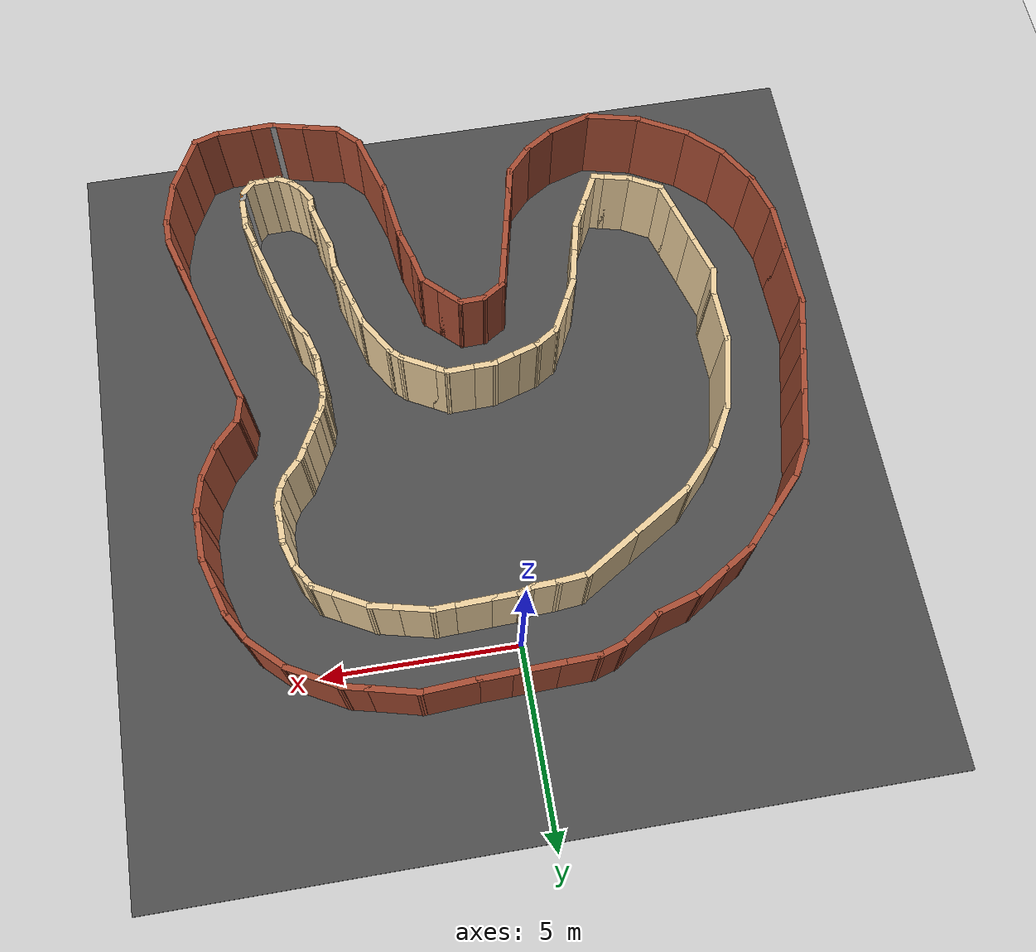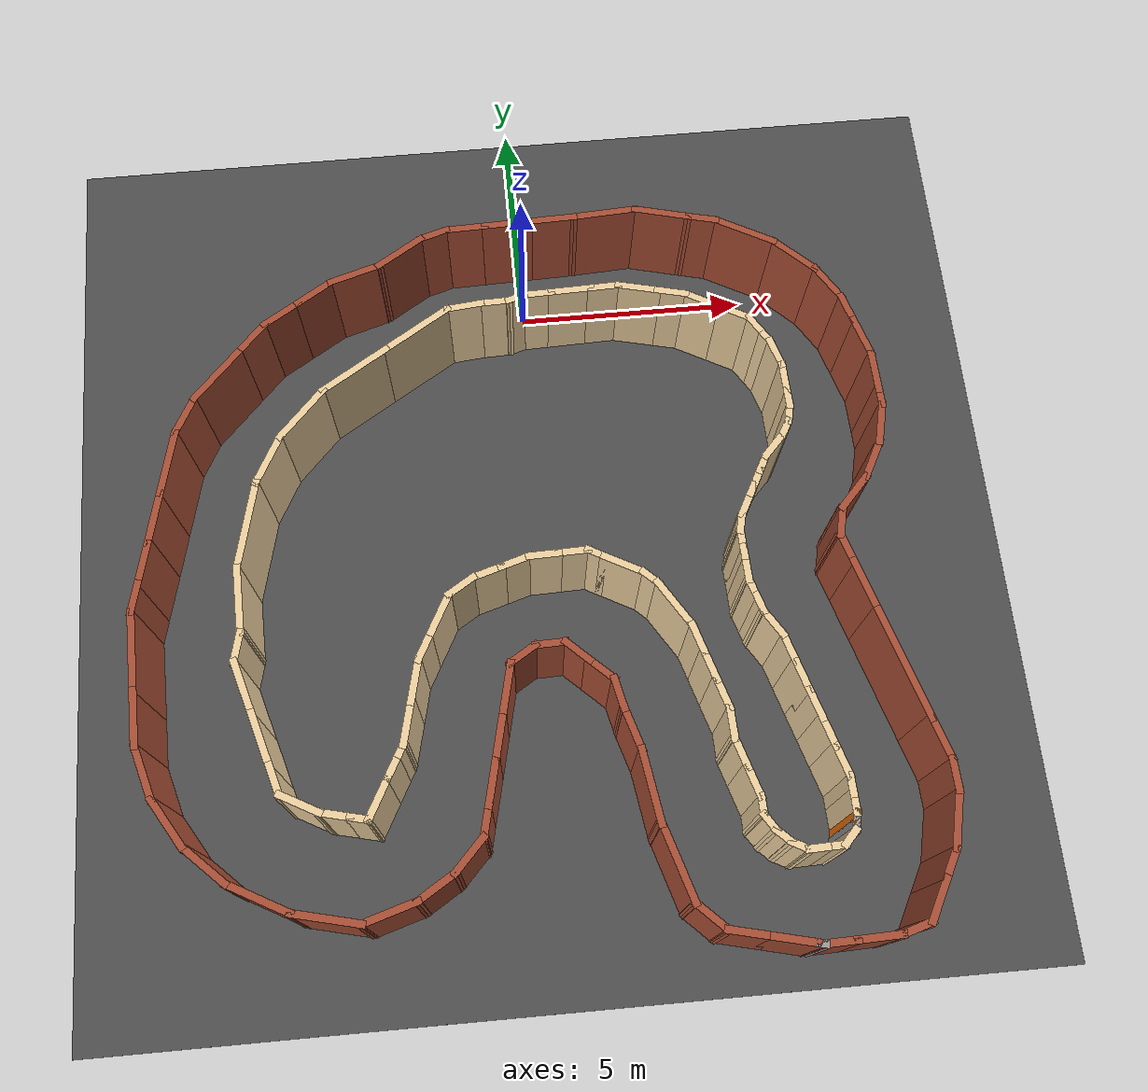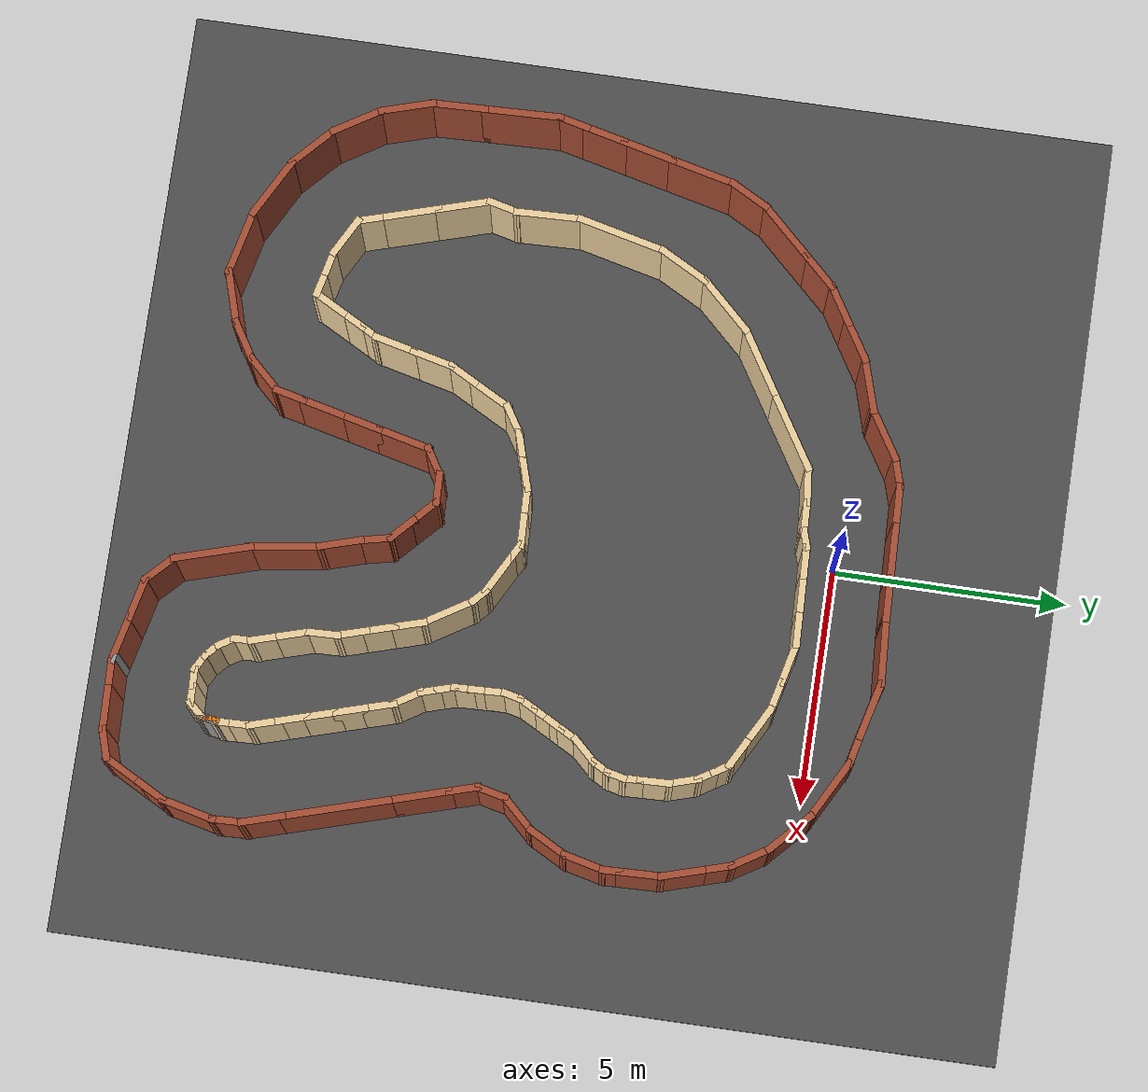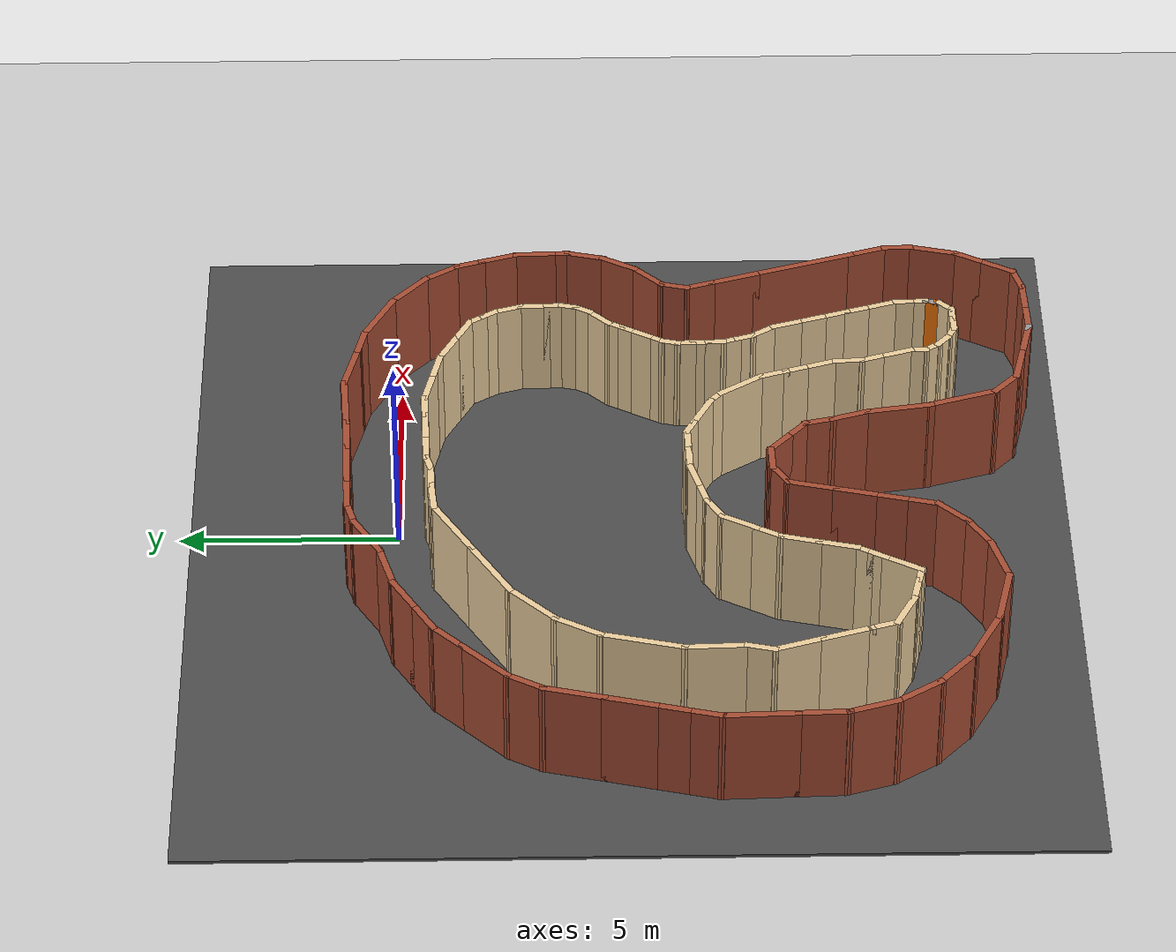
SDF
<sdf version="1.7">
 <world name="default">
  <light name="sun" type="directional">
   <pose>0 0 10 0 -0 0</pose>
   <diffuse>0.8 0.8 0.8 1</diffuse>
   <specular>0.2 0.2 0.2 1</specular>
   <attenuation>
    <range>1000</range>
    <constant>0.9</constant>
    <linear>0.01</linear>
    <quadratic>0.001</quadratic>
   </attenuation>
   <direction>-0.5 0.1 -0.9</direction>
   <spot><inner_angle>0</inner_angle><outer_angle>0</outer_angle><falloff>0</falloff></spot>
  </light>
  <model name="ground_plane">
   <static>1</static>
   <link name="link">
    <collision name="collision">
     <geometry><plane><normal>0 0 1</normal><size>100 100</size></plane></geometry>
     <surface><friction><ode><mu>100</mu><mu2>50</mu2></ode></friction></surface>
    </collision>
    <visual name="visual">
     <cast_shadows>0</cast_shadows>
     <geometry><plane><normal>0 0 1</normal><size>100 100</size></plane></geometry>
     <material>
      <script><uri>file://media/materials/scripts/gazebo.material</uri><name>Gazebo/Grey</name></script>
     </material>
    </visual>
   </link>
  </model>
  <gravity>0 0 -9.8</gravity>
  <magnetic_field>6e-06 2.3e-05 -4.2e-05</magnetic_field>
  <atmosphere type="adiabatic"/>
  <physics type="ode">
   <max_step_size>0.001</max_step_size>
   <real_time_factor>1</real_time_factor>
   <real_time_update_rate>1000</real_time_update_rate>
  </physics>
  <scene><ambient>0.4 0.4 0.4 1</ambient><background>0.7 0.7 0.7 1</background><shadows>1</shadows></scene>
  <audio><device>default</device></audio>
  <spherical_coordinates>
   <surface_model>EARTH_WGS84</surface_model>
   <latitude_deg>0</latitude_deg>
   <longitude_deg>0</longitude_deg>
   <elevation>0</elevation>
   <heading_deg>0</heading_deg>
  </spherical_coordinates>
  <model name="one">
   <pose>-0.558096 -6.76424 0 0 0 -1.54151</pose>
   <link name="Wall_364">
    <collision name="Wall_364_Collision">
     <geometry><box><size>1.32631 0.15 2.5</size></box></geometry>
     <pose>0 0 1.25 0 -0 0</pose>
    </collision>
    <visual name="Wall_364_Visual">
     <pose>0 0 1.25 0 -0 0</pose>
     <geometry><box><size>1.32631 0.15 2.5</size></box></geometry>
     <material>
      <script><uri>file://media/materials/scripts/gazebo.material</uri><name>Gazebo/Bricks</name></script>
      <ambient>1 1 1 1</ambient>
     </material>
     <meta><layer>0</layer></meta>
    </visual>
    <pose>-7.74423 3.9477 0 0 -0 1.29574</pose>
   </link>
   <link name="Wall_365">
    <collision name="Wall_365_Collision">
     <geometry><box><size>0.75 0.15 2.5</size></box></geometry>
     <pose>0 0 1.25 0 -0 0</pose>
    </collision>
    <visual name="Wall_365_Visual">
     <pose>0 0 1.25 0 -0 0</pose>
     <geometry><box><size>0.75 0.15 2.5</size></box></geometry>
     <material>
      <script><uri>file://media/materials/scripts/gazebo.material</uri><name>Gazebo/Bricks</name></script>
      <ambient>1 1 1 1</ambient>
     </material>
     <meta><layer>0</layer></meta>
    </visual>
    <pose>-7.50685 4.80352 0 0 -0 1.309</pose>
   </link>
   <link name="Wall_366">
    <collision name="Wall_366_Collision">
     <geometry><box><size>1.5 0.15 2.5</size></box></geometry>
     <pose>0 0 1.25 0 -0 0</pose>
    </collision>
    <visual name="Wall_366_Visual">
     <pose>0 0 1.25 0 -0 0</pose>
     <geometry><box><size>1.5 0.15 2.5</size></box></geometry>
     <material>
      <script><uri>file://media/materials/scripts/gazebo.material</uri><name>Gazebo/Bricks</name></script>
      <ambient>1 1 1 1</ambient>
     </material>
     <meta><layer>0</layer></meta>
    </visual>
    <pose>-7.0917 5.67786 0 0 -0 1.0472</pose>
   </link>
   <link name="Wall_367">
    <collision name="Wall_367_Collision">
     <geometry><box><size>1.25 0.15 2.5</size></box></geometry>
     <pose>0 0 1.25 0 -0 0</pose>
    </collision>
    <visual name="Wall_367_Visual">
     <pose>0 0 1.25 0 -0 0</pose>
     <geometry><box><size>1.25 0.15 2.5</size></box></geometry>
     <material>
      <script><uri>file://media/materials/scripts/gazebo.material</uri><name>Gazebo/Bricks</name></script>
      <ambient>1 1 1 1</ambient>
     </material>
     <meta><layer>0</layer></meta>
    </visual>
    <pose>-6.36529 6.65134 0 0 -0 0.785398</pose>
   </link>
   <link name="Wall_368">
    <collision name="Wall_368_Collision">
     <geometry><box><size>1 0.15 2.5</size></box></geometry>
     <pose>0 0 1.25 0 -0 0</pose>
    </collision>
    <visual name="Wall_368_Visual">
     <pose>0 0 1.25 0 -0 0</pose>
     <geometry><box><size>1 0.15 2.5</size></box></geometry>
     <material>
      <script><uri>file://media/materials/scripts/gazebo.material</uri><name>Gazebo/Bricks</name></script>
      <ambient>1 1 1 1</ambient>
     </material>
     <meta><layer>0</layer></meta>
    </visual>
    <pose>-5.60832 7.25275 0 0 -0 0.523599</pose>
   </link>
   <link name="Wall_369">
    <collision name="Wall_369_Collision">
     <geometry><box><size>0.75 0.15 2.5</size></box></geometry>
     <pose>0 0 1.25 0 -0 0</pose>
    </collision>
    <visual name="Wall_369_Visual">
     <pose>0 0 1.25 0 -0 0</pose>
     <geometry><box><size>0.75 0.15 2.5</size></box></geometry>
     <material>
      <script><uri>file://media/materials/scripts/gazebo.material</uri><name>Gazebo/Bricks</name></script>
      <ambient>1 1 1 1</ambient>
     </material>
     <meta><layer>0</layer></meta>
    </visual>
    <pose>-4.95048 7.54289 0 0 -0 0.261799</pose>
   </link>
   <link name="Wall_370">
    <collision name="Wall_370_Collision">
     <geometry><box><size>1 0.15 2.5</size></box></geometry>
     <pose>0 0 1.25 0 -0 0</pose>
    </collision>
    <visual name="Wall_370_Visual">
     <pose>0 0 1.25 0 -0 0</pose>
     <geometry><box><size>1 0.15 2.5</size></box></geometry>
     <material>
      <script><uri>file://media/materials/scripts/gazebo.material</uri><name>Gazebo/Bricks</name></script>
      <ambient>1 1 1 1</ambient>
     </material>
     <meta><layer>0</layer></meta>
    </visual>
    <pose>-4.25019 7.73054 0 0 -0 0.261799</pose>
   </link>
   <link name="Wall_371">
    <collision name="Wall_371_Collision">
     <geometry><box><size>1 0.15 2.5</size></box></geometry>
     <pose>0 0 1.25 0 -0 0</pose>
    </collision>
    <visual name="Wall_371_Visual">
     <pose>0 0 1.25 0 -0 0</pose>
     <geometry><box><size>1 0.15 2.5</size></box></geometry>
     <material>
      <script><uri>file://media/materials/scripts/gazebo.material</uri><name>Gazebo/Bricks</name></script>
      <ambient>1 1 1 1</ambient>
     </material>
     <meta><layer>0</layer></meta>
    </visual>
    <pose>-3.41467 7.84054 0 0 -0 0</pose>
   </link>
   <link name="Wall_372">
    <collision name="Wall_372_Collision">
     <geometry><box><size>0.5 0.15 2.5</size></box></geometry>
     <pose>0 0 1.25 0 -0 0</pose>
    </collision>
    <visual name="Wall_372_Visual">
     <pose>0 0 1.25 0 -0 0</pose>
     <geometry><box><size>0.5 0.15 2.5</size></box></geometry>
     <material>
      <script><uri>file://media/materials/scripts/gazebo.material</uri><name>Gazebo/Bricks</name></script>
      <ambient>1 1 1 1</ambient>
     </material>
     <meta><layer>0</layer></meta>
    </visual>
    <pose>-2.81467 7.84054 0 0 -0 0</pose>
   </link>
   <link name="Wall_373">
    <collision name="Wall_373_Collision">
     <geometry><box><size>1 0.15 2.5</size></box></geometry>
     <pose>0 0 1.25 0 -0 0</pose>
    </collision>
    <visual name="Wall_373_Visual">
     <pose>0 0 1.25 0 -0 0</pose>
     <geometry><box><size>1 0.15 2.5</size></box></geometry>
     <material>
      <script><uri>file://media/materials/scripts/gazebo.material</uri><name>Gazebo/Bricks</name></script>
      <ambient>1 1 1 1</ambient>
     </material>
     <meta><layer>0</layer></meta>
    </visual>
    <pose>-2.22915 7.73054 0 0 -0 -0.261799</pose>
   </link>
   <link name="Wall_374">
    <collision name="Wall_374_Collision">
     <geometry><box><size>1 0.15 2.5</size></box></geometry>
     <pose>0 0 1.25 0 -0 0</pose>
    </collision>
    <visual name="Wall_374_Visual">
     <pose>0 0 1.25 0 -0 0</pose>
     <geometry><box><size>1 0.15 2.5</size></box></geometry>
     <material>
      <script><uri>file://media/materials/scripts/gazebo.material</uri><name>Gazebo/Bricks</name></script>
      <ambient>1 1 1 1</ambient>
     </material>
     <meta><layer>0</layer></meta>
    </visual>
    <pose>-1.45057 7.40804 0 0 -0 -0.523599</pose>
   </link>
   <link name="Wall_375">
    <collision name="Wall_375_Collision">
     <geometry><box><size>1 0.15 2.5</size></box></geometry>
     <pose>0 0 1.25 0 -0 0</pose>
    </collision>
    <visual name="Wall_375_Visual">
     <pose>0 0 1.25 0 -0 0</pose>
     <geometry><box><size>1 0.15 2.5</size></box></geometry>
     <material>
      <script><uri>file://media/materials/scripts/gazebo.material</uri><name>Gazebo/Bricks</name></script>
      <ambient>1 1 1 1</ambient>
     </material>
     <meta><layer>0</layer></meta>
    </visual>
    <pose>-0.781989 6.89502 0 0 -0 -0.785398</pose>
   </link>
   <link name="Wall_376">
    <collision name="Wall_376_Collision">
     <geometry><box><size>0.75 0.15 2.5</size></box></geometry>
     <pose>0 0 1.25 0 -0 0</pose>
    </collision>
    <visual name="Wall_376_Visual">
     <pose>0 0 1.25 0 -0 0</pose>
     <geometry><box><size>0.75 0.15 2.5</size></box></geometry>
     <material>
      <script><uri>file://media/materials/scripts/gazebo.material</uri><name>Gazebo/Bricks</name></script>
      <ambient>1 1 1 1</ambient>
     </material>
     <meta><layer>0</layer></meta>
    </visual>
    <pose>-0.191691 6.51685 0 0 -0 -0.261799</pose>
   </link>
   <link name="Wall_377">
    <collision name="Wall_377_Collision">
     <geometry><box><size>0.75 0.15 2.5</size></box></geometry>
     <pose>0 0 1.25 0 -0 0</pose>
    </collision>
    <visual name="Wall_377_Visual">
     <pose>0 0 1.25 0 -0 0</pose>
     <geometry><box><size>0.75 0.15 2.5</size></box></geometry>
     <material>
      <script><uri>file://media/materials/scripts/gazebo.material</uri><name>Gazebo/Bricks</name></script>
      <ambient>1 1 1 1</ambient>
     </material>
     <meta><layer>0</layer></meta>
    </visual>
    <pose>0.387865 6.51685 0 0 -0 0.261799</pose>
   </link>
   <link name="Wall_378">
    <collision name="Wall_378_Collision">
     <geometry><box><size>1.25 0.15 2.5</size></box></geometry>
     <pose>0 0 1.25 0 -0 0</pose>
    </collision>
    <visual name="Wall_378_Visual">
     <pose>0 0 1.25 0 -0 0</pose>
     <geometry><box><size>1.25 0.15 2.5</size></box></geometry>
     <material>
      <script><uri>file://media/materials/scripts/gazebo.material</uri><name>Gazebo/Bricks</name></script>
      <ambient>1 1 1 1</ambient>
     </material>
     <meta><layer>0</layer></meta>
    </visual>
    <pose>1.2089 6.73685 0 0 -0 0.261799</pose>
   </link>
   <link name="Wall_379">
    <collision name="Wall_379_Collision">
     <geometry><box><size>2.5 0.15 2.5</size></box></geometry>
     <pose>0 0 1.25 0 -0 0</pose>
    </collision>
    <visual name="Wall_379_Visual">
     <pose>0 0 1.25 0 -0 0</pose>
     <geometry><box><size>2.5 0.15 2.5</size></box></geometry>
     <material>
      <script><uri>file://media/materials/scripts/gazebo.material</uri><name>Gazebo/Bricks</name></script>
      <ambient>1 1 1 1</ambient>
     </material>
     <meta><layer>0</layer></meta>
    </visual>
    <pose>2.87512 7.18331 0 0 -0 0.261799</pose>
   </link>
   <link name="Wall_380">
    <collision name="Wall_380_Collision">
     <geometry><box><size>1 0.15 2.5</size></box></geometry>
     <pose>0 0 1.25 0 -0 0</pose>
    </collision>
    <visual name="Wall_380_Visual">
     <pose>0 0 1.25 0 -0 0</pose>
     <geometry><box><size>1 0.15 2.5</size></box></geometry>
     <material>
      <script><uri>file://media/materials/scripts/gazebo.material</uri><name>Gazebo/Bricks</name></script>
      <ambient>1 1 1 1</ambient>
     </material>
     <meta><layer>0</layer></meta>
    </visual>
    <pose>4.42061 7.59742 0 0 -0 0.261799</pose>
   </link>
   <link name="Wall_381">
    <collision name="Wall_381_Collision">
     <geometry><box><size>0.75 0.15 2.5</size></box></geometry>
     <pose>0 0 1.25 0 -0 0</pose>
    </collision>
    <visual name="Wall_381_Visual">
     <pose>0 0 1.25 0 -0 0</pose>
     <geometry><box><size>0.75 0.15 2.5</size></box></geometry>
     <material>
      <script><uri>file://media/materials/scripts/gazebo.material</uri><name>Gazebo/Bricks</name></script>
      <ambient>1 1 1 1</ambient>
     </material>
     <meta><layer>0</layer></meta>
    </visual>
    <pose>5.13112 7.70742 0 0 -0 0</pose>
   </link>
   <link name="Wall_382">
    <collision name="Wall_382_Collision">
     <geometry><box><size>1.25 0.15 2.5</size></box></geometry>
     <pose>0 0 1.25 0 -0 0</pose>
    </collision>
    <visual name="Wall_382_Visual">
     <pose>0 0 1.25 0 -0 0</pose>
     <geometry><box><size>1.25 0.15 2.5</size></box></geometry>
     <material>
      <script><uri>file://media/materials/scripts/gazebo.material</uri><name>Gazebo/Bricks</name></script>
      <ambient>1 1 1 1</ambient>
     </material>
     <meta><layer>0</layer></meta>
    </visual>
    <pose>5.96238 7.56507 0 0 -0 -0.261799</pose>
   </link>
   <link name="Wall_383">
    <collision name="Wall_383_Collision">
     <geometry><box><size>0.75 0.15 2.5</size></box></geometry>
     <pose>0 0 1.25 0 -0 0</pose>
    </collision>
    <visual name="Wall_383_Visual">
     <pose>0 0 1.25 0 -0 0</pose>
     <geometry><box><size>0.75 0.15 2.5</size></box></geometry>
     <material>
      <script><uri>file://media/materials/scripts/gazebo.material</uri><name>Gazebo/Bricks</name></script>
      <ambient>1 1 1 1</ambient>
     </material>
     <meta><layer>0</layer></meta>
    </visual>
    <pose>6.75345 7.27272 0 0 -0 -0.523599</pose>
   </link>
   <link name="Wall_384">
    <collision name="Wall_384_Collision">
     <geometry><box><size>1 0.15 2.5</size></box></geometry>
     <pose>0 0 1.25 0 -0 0</pose>
    </collision>
    <visual name="Wall_384_Visual">
     <pose>0 0 1.25 0 -0 0</pose>
     <geometry><box><size>1 0.15 2.5</size></box></geometry>
     <material>
      <script><uri>file://media/materials/scripts/gazebo.material</uri><name>Gazebo/Bricks</name></script>
      <ambient>1 1 1 1</ambient>
     </material>
     <meta><layer>0</layer></meta>
    </visual>
    <pose>7.38132 6.91022 0 0 -0 -0.523599</pose>
   </link>
   <link name="Wall_385">
    <collision name="Wall_385_Collision">
     <geometry><box><size>0.75 0.15 2.5</size></box></geometry>
     <pose>0 0 1.25 0 -0 0</pose>
    </collision>
    <visual name="Wall_385_Visual">
     <pose>0 0 1.25 0 -0 0</pose>
     <geometry><box><size>0.75 0.15 2.5</size></box></geometry>
     <material>
      <script><uri>file://media/materials/scripts/gazebo.material</uri><name>Gazebo/Bricks</name></script>
      <ambient>1 1 1 1</ambient>
     </material>
     <meta><layer>0</layer></meta>
    </visual>
    <pose>7.82702 6.40794 0 0 -0 -1.309</pose>
   </link>
   <link name="Wall_386">
    <collision name="Wall_386_Collision">
     <geometry><box><size>1 0.15 2.5</size></box></geometry>
     <pose>0 0 1.25 0 -0 0</pose>
    </collision>
    <visual name="Wall_386_Visual">
     <pose>0 0 1.25 0 -0 0</pose>
     <geometry><box><size>1 0.15 2.5</size></box></geometry>
     <material>
      <script><uri>file://media/materials/scripts/gazebo.material</uri><name>Gazebo/Bricks</name></script>
      <ambient>1 1 1 1</ambient>
     </material>
     <meta><layer>0</layer></meta>
    </visual>
    <pose>7.90467 5.69316 0 0 -0 -1.5708</pose>
   </link>
   <link name="Wall_387">
    <collision name="Wall_387_Collision">
     <geometry><box><size>0.75 0.15 2.5</size></box></geometry>
     <pose>0 0 1.25 0 -0 0</pose>
    </collision>
    <visual name="Wall_387_Visual">
     <pose>0 0 1.25 0 -0 0</pose>
     <geometry><box><size>0.75 0.15 2.5</size></box></geometry>
     <material>
      <script><uri>file://media/materials/scripts/gazebo.material</uri><name>Gazebo/Bricks</name></script>
      <ambient>1 1 1 1</ambient>
     </material>
     <meta><layer>0</layer></meta>
    </visual>
    <pose>7.90467 4.96816 0 0 -0 -1.5708</pose>
   </link>
   <link name="Wall_388">
    <collision name="Wall_388_Collision">
     <geometry><box><size>0.25 0.15 2.5</size></box></geometry>
     <pose>0 0 1.25 0 -0 0</pose>
    </collision>
    <visual name="Wall_388_Visual">
     <pose>0 0 1.25 0 -0 0</pose>
     <geometry><box><size>0.25 0.15 2.5</size></box></geometry>
     <material>
      <script><uri>file://media/materials/scripts/gazebo.material</uri><name>Gazebo/Grey</name></script>
      <ambient>1 1 1 1</ambient>
     </material>
     <meta><layer>0</layer></meta>
    </visual>
    <pose>7.89173 4.61987 0 0 -0 -1.8326</pose>
   </link>
   <link name="Wall_389">
    <collision name="Wall_389_Collision">
     <geometry><box><size>1 0.15 2.5</size></box></geometry>
     <pose>0 0 1.25 0 -0 0</pose>
    </collision>
    <visual name="Wall_389_Visual">
     <pose>0 0 1.25 0 -0 0</pose>
     <geometry><box><size>1 0.15 2.5</size></box></geometry>
     <material>
      <script><uri>file://media/materials/scripts/gazebo.material</uri><name>Gazebo/Bricks</name></script>
      <ambient>1 1 1 1</ambient>
     </material>
     <meta><layer>0</layer></meta>
    </visual>
    <pose>7.76879 4.16105 0 0 -0 -1.8326</pose>
   </link>
   <link name="Wall_390">
    <collision name="Wall_390_Collision">
     <geometry><box><size>1 0.15 2.5</size></box></geometry>
     <pose>0 0 1.25 0 -0 0</pose>
    </collision>
    <visual name="Wall_390_Visual">
     <pose>0 0 1.25 0 -0 0</pose>
     <geometry><box><size>1 0.15 2.5</size></box></geometry>
     <material>
      <script><uri>file://media/materials/scripts/gazebo.material</uri><name>Gazebo/Bricks</name></script>
      <ambient>1 1 1 1</ambient>
     </material>
     <meta><layer>0</layer></meta>
    </visual>
    <pose>7.54879 3.34002 0 0 -0 -1.8326</pose>
   </link>
   <link name="Wall_391">
    <collision name="Wall_391_Collision">
     <geometry><box><size>0.889556 0.15 2.5</size></box></geometry>
     <pose>0 0 1.25 0 -0 0</pose>
    </collision>
    <visual name="Wall_391_Visual">
     <pose>0 0 1.25 0 -0 0</pose>
     <geometry><box><size>0.889556 0.15 2.5</size></box></geometry>
     <material>
      <script><uri>file://media/materials/scripts/gazebo.material</uri><name>Gazebo/Bricks</name></script>
      <ambient>1 1 1 1</ambient>
     </material>
     <meta><layer>0</layer></meta>
    </visual>
    <pose>7.17195 2.67351 0 0 -0 -2.37696</pose>
   </link>
   <link name="Wall_392">
    <collision name="Wall_392_Collision">
     <geometry><box><size>1.75 0.15 2.5</size></box></geometry>
     <pose>0 0 1.25 0 -0 0</pose>
    </collision>
    <visual name="Wall_392_Visual">
     <pose>0 0 1.25 0 -0 0</pose>
     <geometry><box><size>1.75 0.15 2.5</size></box></geometry>
     <material>
      <script><uri>file://media/materials/scripts/gazebo.material</uri><name>Gazebo/Bricks</name></script>
      <ambient>1 1 1 1</ambient>
     </material>
     <meta><layer>0</layer></meta>
    </visual>
    <pose>6.13237 2.21047 0 0 -0 -2.87979</pose>
   </link>
   <link name="Wall_393">
    <collision name="Wall_393_Collision">
     <geometry><box><size>1.62119 0.15 2.5</size></box></geometry>
     <pose>0 0 1.25 0 -0 0</pose>
    </collision>
    <visual name="Wall_393_Visual">
     <pose>0 0 1.25 0 -0 0</pose>
     <geometry><box><size>1.62119 0.15 2.5</size></box></geometry>
     <material>
      <script><uri>file://media/materials/scripts/gazebo.material</uri><name>Gazebo/Bricks</name></script>
      <ambient>1 1 1 1</ambient>
     </material>
     <meta><layer>0</layer></meta>
    </visual>
    <pose>4.66397 1.91645 0 0 -0 -3.0231</pose>
   </link>
   <link name="Wall_394">
    <collision name="Wall_394_Collision">
     <geometry><box><size>1 0.15 2.5</size></box></geometry>
     <pose>0 0 1.25 0 -0 0</pose>
    </collision>
    <visual name="Wall_394_Visual">
     <pose>0 0 1.25 0 -0 0</pose>
     <geometry><box><size>1 0.15 2.5</size></box></geometry>
     <material>
      <script><uri>file://media/materials/scripts/gazebo.material</uri><name>Gazebo/Bricks</name></script>
      <ambient>1 1 1 1</ambient>
     </material>
     <meta><layer>0</layer></meta>
    </visual>
    <pose>3.52302 1.7195 0 0 -0 -2.87979</pose>
   </link>
   <link name="Wall_397">
    <collision name="Wall_397_Collision">
     <geometry><box><size>1 0.15 2.5</size></box></geometry>
     <pose>0 0 1.25 0 -0 0</pose>
    </collision>
    <visual name="Wall_397_Visual">
     <pose>0 0 1.25 0 -0 0</pose>
     <geometry><box><size>1 0.15 2.5</size></box></geometry>
     <material>
      <script><uri>file://media/materials/scripts/gazebo.material</uri><name>Gazebo/Bricks</name></script>
      <ambient>1 1 1 1</ambient>
     </material>
     <meta><layer>0</layer></meta>
    </visual>
    <pose>-7.86919 -0.35856 0 0 -0 1.5708</pose>
   </link>
   <link name="Wall_398">
    <collision name="Wall_398_Collision">
     <geometry><box><size>1.25 0.15 2.5</size></box></geometry>
     <pose>0 0 1.25 0 -0 0</pose>
    </collision>
    <visual name="Wall_398_Visual">
     <pose>0 0 1.25 0 -0 0</pose>
     <geometry><box><size>1.25 0.15 2.5</size></box></geometry>
     <material>
      <script><uri>file://media/materials/scripts/gazebo.material</uri><name>Gazebo/Bricks</name></script>
      <ambient>1 1 1 1</ambient>
     </material>
     <meta><layer>0</layer></meta>
    </visual>
    <pose>-7.86919 0.61644 0 0 -0 1.5708</pose>
   </link>
   <link name="Wall_399">
    <collision name="Wall_399_Collision">
     <geometry><box><size>1 0.15 2.5</size></box></geometry>
     <pose>0 0 1.25 0 -0 0</pose>
    </collision>
    <visual name="Wall_399_Visual">
     <pose>0 0 1.25 0 -0 0</pose>
     <geometry><box><size>1 0.15 2.5</size></box></geometry>
     <material>
      <script><uri>file://media/materials/scripts/gazebo.material</uri><name>Gazebo/Bricks</name></script>
      <ambient>1 1 1 1</ambient>
     </material>
     <meta><layer>0</layer></meta>
    </visual>
    <pose>-7.86919 1.59144 0 0 -0 1.5708</pose>
   </link>
   <link name="Wall_400">
    <collision name="Wall_400_Collision">
     <geometry><box><size>1.51566 0.15 2.5</size></box></geometry>
     <pose>0 0 1.25 0 -0 0</pose>
    </collision>
    <visual name="Wall_400_Visual">
     <pose>0 0 1.25 0 -0 0</pose>
     <geometry><box><size>1.51566 0.15 2.5</size></box></geometry>
     <material>
      <script><uri>file://media/materials/scripts/gazebo.material</uri><name>Gazebo/Bricks</name></script>
      <ambient>1 1 1 1</ambient>
     </material>
     <meta><layer>0</layer></meta>
    </visual>
    <pose>-7.88658 2.69905 0 0 -0 1.59627</pose>
   </link>
   <link name="Wall_402">
    <collision name="Wall_402_Collision">
     <geometry><box><size>0.75 0.15 2.5</size></box></geometry>
     <pose>0 0 1.25 0 -0 0</pose>
    </collision>
    <visual name="Wall_402_Visual">
     <pose>0 0 1.25 0 -0 0</pose>
     <geometry><box><size>0.75 0.15 2.5</size></box></geometry>
     <material>
      <script><uri>file://media/materials/scripts/gazebo.material</uri><name>Gazebo/Bricks</name></script>
      <ambient>1 1 1 1</ambient>
     </material>
     <meta><layer>0</layer></meta>
    </visual>
    <pose>-7.79155 -1.07334 0 0 -0 -1.309</pose>
   </link>
   <link name="Wall_403">
    <collision name="Wall_403_Collision">
     <geometry><box><size>1.25 0.15 2.5</size></box></geometry>
     <pose>0 0 1.25 0 -0 0</pose>
    </collision>
    <visual name="Wall_403_Visual">
     <pose>0 0 1.25 0 -0 0</pose>
     <geometry><box><size>1.25 0.15 2.5</size></box></geometry>
     <material>
      <script><uri>file://media/materials/scripts/gazebo.material</uri><name>Gazebo/Bricks</name></script>
      <ambient>1 1 1 1</ambient>
     </material>
     <meta><layer>0</layer></meta>
    </visual>
    <pose>-7.4389 -1.83943 0 0 -0 -1.0472</pose>
   </link>
   <link name="Wall_404">
    <collision name="Wall_404_Collision">
     <geometry><box><size>1.25 0.15 2.5</size></box></geometry>
     <pose>0 0 1.25 0 -0 0</pose>
    </collision>
    <visual name="Wall_404_Visual">
     <pose>0 0 1.25 0 -0 0</pose>
     <geometry><box><size>1.25 0.15 2.5</size></box></geometry>
     <material>
      <script><uri>file://media/materials/scripts/gazebo.material</uri><name>Gazebo/Bricks</name></script>
      <ambient>1 1 1 1</ambient>
     </material>
     <meta><layer>0</layer></meta>
    </visual>
    <pose>-7.02155 -2.847 0 0 -0 -1.309</pose>
   </link>
   <link name="Wall_405">
    <collision name="Wall_405_Collision">
     <geometry><box><size>1 0.15 2.5</size></box></geometry>
     <pose>0 0 1.25 0 -0 0</pose>
    </collision>
    <visual name="Wall_405_Visual">
     <pose>0 0 1.25 0 -0 0</pose>
     <geometry><box><size>1 0.15 2.5</size></box></geometry>
     <material>
      <script><uri>file://media/materials/scripts/gazebo.material</uri><name>Gazebo/Bricks</name></script>
      <ambient>1 1 1 1</ambient>
     </material>
     <meta><layer>0</layer></meta>
    </visual>
    <pose>-6.6667 -3.74632 0 0 -0 -1.0472</pose>
   </link>
   <link name="Wall_406">
    <collision name="Wall_406_Collision">
     <geometry><box><size>1 0.15 2.5</size></box></geometry>
     <pose>0 0 1.25 0 -0 0</pose>
    </collision>
    <visual name="Wall_406_Visual">
     <pose>0 0 1.25 0 -0 0</pose>
     <geometry><box><size>1 0.15 2.5</size></box></geometry>
     <material>
      <script><uri>file://media/materials/scripts/gazebo.material</uri><name>Gazebo/Bricks</name></script>
      <ambient>1 1 1 1</ambient>
     </material>
     <meta><layer>0</layer></meta>
    </visual>
    <pose>-6.2417 -4.48245 0 0 -0 -1.0472</pose>
   </link>
   <link name="Wall_407">
    <collision name="Wall_407_Collision">
     <geometry><box><size>1 0.15 2.5</size></box></geometry>
     <pose>0 0 1.25 0 -0 0</pose>
    </collision>
    <visual name="Wall_407_Visual">
     <pose>0 0 1.25 0 -0 0</pose>
     <geometry><box><size>1 0.15 2.5</size></box></geometry>
     <material>
      <script><uri>file://media/materials/scripts/gazebo.material</uri><name>Gazebo/Bricks</name></script>
      <ambient>1 1 1 1</ambient>
     </material>
     <meta><layer>0</layer></meta>
    </visual>
    <pose>-5.72868 -5.15103 0 0 -0 -0.785398</pose>
   </link>
   <link name="Wall_408">
    <collision name="Wall_408_Collision">
     <geometry><box><size>1.5 0.15 2.5</size></box></geometry>
     <pose>0 0 1.25 0 -0 0</pose>
    </collision>
    <visual name="Wall_408_Visual">
     <pose>0 0 1.25 0 -0 0</pose>
     <geometry><box><size>1.5 0.15 2.5</size></box></geometry>
     <material>
      <script><uri>file://media/materials/scripts/gazebo.material</uri><name>Gazebo/Bricks</name></script>
      <ambient>1 1 1 1</ambient>
     </material>
     <meta><layer>0</layer></meta>
    </visual>
    <pose>-4.95086 -5.92884 0 0 -0 -0.785398</pose>
   </link>
   <link name="Wall_409">
    <collision name="Wall_409_Collision">
     <geometry><box><size>1 0.15 2.5</size></box></geometry>
     <pose>0 0 1.25 0 -0 0</pose>
    </collision>
    <visual name="Wall_409_Visual">
     <pose>0 0 1.25 0 -0 0</pose>
     <geometry><box><size>1 0.15 2.5</size></box></geometry>
     <material>
      <script><uri>file://media/materials/scripts/gazebo.material</uri><name>Gazebo/Bricks</name></script>
      <ambient>1 1 1 1</ambient>
     </material>
     <meta><layer>0</layer></meta>
    </visual>
    <pose>-4.1055 -6.61864 0 0 -0 -0.523599</pose>
   </link>
   <link name="Wall_410">
    <collision name="Wall_410_Collision">
     <geometry><box><size>1.5 0.15 2.5</size></box></geometry>
     <pose>0 0 1.25 0 -0 0</pose>
    </collision>
    <visual name="Wall_410_Visual">
     <pose>0 0 1.25 0 -0 0</pose>
     <geometry><box><size>1.5 0.15 2.5</size></box></geometry>
     <material>
      <script><uri>file://media/materials/scripts/gazebo.material</uri><name>Gazebo/Bricks</name></script>
      <ambient>1 1 1 1</ambient>
     </material>
     <meta><layer>0</layer></meta>
    </visual>
    <pose>-3.08544 -7.00584 0 0 -0 -0.261799</pose>
   </link>
   <link name="Wall_411">
    <collision name="Wall_411_Collision">
     <geometry><box><size>1.25 0.15 2.5</size></box></geometry>
     <pose>0 0 1.25 0 -0 0</pose>
    </collision>
    <visual name="Wall_411_Visual">
     <pose>0 0 1.25 0 -0 0</pose>
     <geometry><box><size>1.25 0.15 2.5</size></box></geometry>
     <material>
      <script><uri>file://media/materials/scripts/gazebo.material</uri><name>Gazebo/Bricks</name></script>
      <ambient>1 1 1 1</ambient>
     </material>
     <meta><layer>0</layer></meta>
    </visual>
    <pose>-1.90218 -7.3229 0 0 -0 -0.261799</pose>
   </link>
   <link name="Wall_412">
    <collision name="Wall_412_Collision">
     <geometry><box><size>1 0.15 2.5</size></box></geometry>
     <pose>0 0 1.25 0 -0 0</pose>
    </collision>
    <visual name="Wall_412_Visual">
     <pose>0 0 1.25 0 -0 0</pose>
     <geometry><box><size>1 0.15 2.5</size></box></geometry>
     <material>
      <script><uri>file://media/materials/scripts/gazebo.material</uri><name>Gazebo/Bricks</name></script>
      <ambient>1 1 1 1</ambient>
     </material>
     <meta><layer>0</layer></meta>
    </visual>
    <pose>-0.960406 -7.57524 0 0 -0 -0.261799</pose>
   </link>
   <link name="Wall_413">
    <collision name="Wall_413_Collision">
     <geometry><box><size>0.75 0.15 2.5</size></box></geometry>
     <pose>0 0 1.25 0 -0 0</pose>
    </collision>
    <visual name="Wall_413_Visual">
     <pose>0 0 1.25 0 -0 0</pose>
     <geometry><box><size>0.75 0.15 2.5</size></box></geometry>
     <material>
      <script><uri>file://media/materials/scripts/gazebo.material</uri><name>Gazebo/Bricks</name></script>
      <ambient>1 1 1 1</ambient>
     </material>
     <meta><layer>0</layer></meta>
    </visual>
    <pose>-0.26011 -7.76289 0 0 -0 -0.261799</pose>
   </link>
   <link name="Wall_414">
    <collision name="Wall_414_Collision">
     <geometry><box><size>1.75 0.15 2.5</size></box></geometry>
     <pose>0 0 1.25 0 -0 0</pose>
    </collision>
    <visual name="Wall_414_Visual">
     <pose>0 0 1.25 0 -0 0</pose>
     <geometry><box><size>1.75 0.15 2.5</size></box></geometry>
     <material>
      <script><uri>file://media/materials/scripts/gazebo.material</uri><name>Gazebo/Bricks</name></script>
      <ambient>1 1 1 1</ambient>
     </material>
     <meta><layer>0</layer></meta>
    </visual>
    <pose>0.829668 -7.84054 0 0 -0 0</pose>
   </link>
   <link name="Wall_415">
    <collision name="Wall_415_Collision">
     <geometry><box><size>1.25 0.15 2.5</size></box></geometry>
     <pose>0 0 1.25 0 -0 0</pose>
    </collision>
    <visual name="Wall_415_Visual">
     <pose>0 0 1.25 0 -0 0</pose>
     <geometry><box><size>1.25 0.15 2.5</size></box></geometry>
     <material>
      <script><uri>file://media/materials/scripts/gazebo.material</uri><name>Gazebo/Bricks</name></script>
      <ambient>1 1 1 1</ambient>
     </material>
     <meta><layer>0</layer></meta>
    </visual>
    <pose>2.17967 -7.84054 0 0 -0 0</pose>
   </link>
   <link name="Wall_416">
    <collision name="Wall_416_Collision">
     <geometry><box><size>1.25 0.15 2.5</size></box></geometry>
     <pose>0 0 1.25 0 -0 0</pose>
    </collision>
    <visual name="Wall_416_Visual">
     <pose>0 0 1.25 0 -0 0</pose>
     <geometry><box><size>1.25 0.15 2.5</size></box></geometry>
     <material>
      <script><uri>file://media/materials/scripts/gazebo.material</uri><name>Gazebo/Bricks</name></script>
      <ambient>1 1 1 1</ambient>
     </material>
     <meta><layer>0</layer></meta>
    </visual>
    <pose>3.26093 -7.69818 0 0 -0 0.261799</pose>
   </link>
   <link name="Wall_417">
    <collision name="Wall_417_Collision">
     <geometry><box><size>1.25 0.15 2.5</size></box></geometry>
     <pose>0 0 1.25 0 -0 0</pose>
    </collision>
    <visual name="Wall_417_Visual">
     <pose>0 0 1.25 0 -0 0</pose>
     <geometry><box><size>1.25 0.15 2.5</size></box></geometry>
     <material>
      <script><uri>file://media/materials/scripts/gazebo.material</uri><name>Gazebo/Bricks</name></script>
      <ambient>1 1 1 1</ambient>
     </material>
     <meta><layer>0</layer></meta>
    </visual>
    <pose>4.2685 -7.28083 0 0 -0 0.523599</pose>
   </link>
   <link name="Wall_418">
    <collision name="Wall_418_Collision">
     <geometry><box><size>1.25 0.15 2.5</size></box></geometry>
     <pose>0 0 1.25 0 -0 0</pose>
    </collision>
    <visual name="Wall_418_Visual">
     <pose>0 0 1.25 0 -0 0</pose>
     <geometry><box><size>1.25 0.15 2.5</size></box></geometry>
     <material>
      <script><uri>file://media/materials/scripts/gazebo.material</uri><name>Gazebo/Bricks</name></script>
      <ambient>1 1 1 1</ambient>
     </material>
     <meta><layer>0</layer></meta>
    </visual>
    <pose>5.13372 -6.61693 0 0 -0 0.785398</pose>
   </link>
   <link name="Wall_419">
    <collision name="Wall_419_Collision">
     <geometry><box><size>1.5 0.15 2.5</size></box></geometry>
     <pose>0 0 1.25 0 -0 0</pose>
    </collision>
    <visual name="Wall_419_Visual">
     <pose>0 0 1.25 0 -0 0</pose>
     <geometry><box><size>1.5 0.15 2.5</size></box></geometry>
     <material>
      <script><uri>file://media/materials/scripts/gazebo.material</uri><name>Gazebo/Bricks</name></script>
      <ambient>1 1 1 1</ambient>
     </material>
     <meta><layer>0</layer></meta>
    </visual>
    <pose>5.86013 -5.64345 0 0 -0 1.0472</pose>
   </link>
   <link name="Wall_420">
    <collision name="Wall_420_Collision">
     <geometry><box><size>1.5 0.15 2.5</size></box></geometry>
     <pose>0 0 1.25 0 -0 0</pose>
    </collision>
    <visual name="Wall_420_Visual">
     <pose>0 0 1.25 0 -0 0</pose>
     <geometry><box><size>1.5 0.15 2.5</size></box></geometry>
     <material>
      <script><uri>file://media/materials/scripts/gazebo.material</uri><name>Gazebo/Bricks</name></script>
      <ambient>1 1 1 1</ambient>
     </material>
     <meta><layer>0</layer></meta>
    </visual>
    <pose>6.37233 -4.40688 0 0 -0 1.309</pose>
   </link>
   <link name="Wall_421">
    <collision name="Wall_421_Collision">
     <geometry><box><size>1.25 0.15 2.5</size></box></geometry>
     <pose>0 0 1.25 0 -0 0</pose>
    </collision>
    <visual name="Wall_421_Visual">
     <pose>0 0 1.25 0 -0 0</pose>
     <geometry><box><size>1.25 0.15 2.5</size></box></geometry>
     <material>
      <script><uri>file://media/materials/scripts/gazebo.material</uri><name>Gazebo/Bricks</name></script>
      <ambient>1 1 1 1</ambient>
     </material>
     <meta><layer>0</layer></meta>
    </visual>
    <pose>6.40469 -3.22362 0 0 -0 1.8326</pose>
   </link>
   <link name="Wall_422">
    <collision name="Wall_422_Collision">
     <geometry><box><size>1 0.15 2.5</size></box></geometry>
     <pose>0 0 1.25 0 -0 0</pose>
    </collision>
    <visual name="Wall_422_Visual">
     <pose>0 0 1.25 0 -0 0</pose>
     <geometry><box><size>1 0.15 2.5</size></box></geometry>
     <material>
      <script><uri>file://media/materials/scripts/gazebo.material</uri><name>Gazebo/Bricks</name></script>
      <ambient>1 1 1 1</ambient>
     </material>
     <meta><layer>0</layer></meta>
    </visual>
    <pose>6.04984 -2.3243 0 0 -0 2.0944</pose>
   </link>
   <link name="Wall_423">
    <collision name="Wall_423_Collision">
     <geometry><box><size>1 0.15 2.5</size></box></geometry>
     <pose>0 0 1.25 0 -0 0</pose>
    </collision>
    <visual name="Wall_423_Visual">
     <pose>0 0 1.25 0 -0 0</pose>
     <geometry><box><size>1 0.15 2.5</size></box></geometry>
     <material>
      <script><uri>file://media/materials/scripts/gazebo.material</uri><name>Gazebo/Bricks</name></script>
      <ambient>1 1 1 1</ambient>
     </material>
     <meta><layer>0</layer></meta>
    </visual>
    <pose>5.53682 -1.65572 0 0 -0 2.35619</pose>
   </link>
   <link name="Wall_424">
    <collision name="Wall_424_Collision">
     <geometry><box><size>0.75 0.15 2.5</size></box></geometry>
     <pose>0 0 1.25 0 -0 0</pose>
    </collision>
    <visual name="Wall_424_Visual">
     <pose>0 0 1.25 0 -0 0</pose>
     <geometry><box><size>0.75 0.15 2.5</size></box></geometry>
     <material>
      <script><uri>file://media/materials/scripts/gazebo.material</uri><name>Gazebo/Bricks</name></script>
      <ambient>1 1 1 1</ambient>
     </material>
     <meta><layer>0</layer></meta>
    </visual>
    <pose>4.94652 -1.27756 0 0 -0 2.87979</pose>
   </link>
   <link name="Wall_425">
    <collision name="Wall_425_Collision">
     <geometry><box><size>1 0.15 2.5</size></box></geometry>
     <pose>0 0 1.25 0 -0 0</pose>
    </collision>
    <visual name="Wall_425_Visual">
     <pose>0 0 1.25 0 -0 0</pose>
     <geometry><box><size>1 0.15 2.5</size></box></geometry>
     <material>
      <script><uri>file://media/materials/scripts/gazebo.material</uri><name>Gazebo/Bricks</name></script>
      <ambient>1 1 1 1</ambient>
     </material>
     <meta><layer>0</layer></meta>
    </visual>
    <pose>4.24622 -1.08991 0 0 -0 2.87979</pose>
   </link>
   <link name="Wall_426">
    <collision name="Wall_426_Collision">
     <geometry><box><size>1 0.15 2.5</size></box></geometry>
     <pose>0 0 1.25 0 -0 0</pose>
    </collision>
    <visual name="Wall_426_Visual">
     <pose>0 0 1.25 0 -0 0</pose>
     <geometry><box><size>1 0.15 2.5</size></box></geometry>
     <material>
      <script><uri>file://media/materials/scripts/gazebo.material</uri><name>Gazebo/Bricks</name></script>
      <ambient>1 1 1 1</ambient>
     </material>
     <meta><layer>0</layer></meta>
    </visual>
    <pose>3.42518 -0.869916 0 0 -0 2.87979</pose>
   </link>
   <link name="Wall_427">
    <collision name="Wall_427_Collision">
     <geometry><box><size>1.25 0.15 2.5</size></box></geometry>
     <pose>0 0 1.25 0 -0 0</pose>
    </collision>
    <visual name="Wall_427_Visual">
     <pose>0 0 1.25 0 -0 0</pose>
     <geometry><box><size>1.25 0.15 2.5</size></box></geometry>
     <material>
      <script><uri>file://media/materials/scripts/gazebo.material</uri><name>Gazebo/Bricks</name></script>
      <ambient>1 1 1 1</ambient>
     </material>
     <meta><layer>0</layer></meta>
    </visual>
    <pose>2.48341 -0.617567 0 0 -0 2.87979</pose>
   </link>
   <link name="Wall_428">
    <collision name="Wall_428_Collision">
     <geometry><box><size>0.75 0.15 2.5</size></box></geometry>
     <pose>0 0 1.25 0 -0 0</pose>
    </collision>
    <visual name="Wall_428_Visual">
     <pose>0 0 1.25 0 -0 0</pose>
     <geometry><box><size>0.75 0.15 2.5</size></box></geometry>
     <material>
      <script><uri>file://media/materials/scripts/gazebo.material</uri><name>Gazebo/Bricks</name></script>
      <ambient>1 1 1 1</ambient>
     </material>
     <meta><layer>0</layer></meta>
    </visual>
    <pose>1.80215 -0.215409 0 0 -0 2.0944</pose>
   </link>
   <link name="Wall_429">
    <collision name="Wall_429_Collision">
     <geometry><box><size>0.75 0.15 2.5</size></box></geometry>
     <pose>0 0 1.25 0 -0 0</pose>
    </collision>
    <visual name="Wall_429_Visual">
     <pose>0 0 1.25 0 -0 0</pose>
     <geometry><box><size>0.75 0.15 2.5</size></box></geometry>
     <material>
      <script><uri>file://media/materials/scripts/gazebo.material</uri><name>Gazebo/Bricks</name></script>
      <ambient>1 1 1 1</ambient>
     </material>
     <meta><layer>0</layer></meta>
    </visual>
    <pose>1.65215 0.344399 0 0 -0 1.5708</pose>
   </link>
   <link name="Wall_430">
    <collision name="Wall_430_Collision">
     <geometry><box><size>0.75 0.15 2.5</size></box></geometry>
     <pose>0 0 1.25 0 -0 0</pose>
    </collision>
    <visual name="Wall_430_Visual">
     <pose>0 0 1.25 0 -0 0</pose>
     <geometry><box><size>0.75 0.15 2.5</size></box></geometry>
     <material>
      <script><uri>file://media/materials/scripts/gazebo.material</uri><name>Gazebo/Bricks</name></script>
      <ambient>1 1 1 1</ambient>
     </material>
     <meta><layer>0</layer></meta>
    </visual>
    <pose>1.86428 0.856531 0 0 -0 0.785398</pose>
   </link>
   <link name="Wall_431">
    <collision name="Wall_431_Collision">
     <geometry><box><size>0.75 0.15 2.5</size></box></geometry>
     <pose>0 0 1.25 0 -0 0</pose>
    </collision>
    <visual name="Wall_431_Visual">
     <pose>0 0 1.25 0 -0 0</pose>
     <geometry><box><size>0.75 0.15 2.5</size></box></geometry>
     <material>
      <script><uri>file://media/materials/scripts/gazebo.material</uri><name>Gazebo/Bricks</name></script>
      <ambient>1 1 1 1</ambient>
     </material>
     <meta><layer>0</layer></meta>
    </visual>
    <pose>2.28854 1.28079 0 0 -0 0.785398</pose>
   </link>
   <link name="Wall_432">
    <collision name="Wall_432_Collision">
     <geometry><box><size>0.772834 0.15 2.5</size></box></geometry>
     <pose>0 0 1.25 0 -0 0</pose>
    </collision>
    <visual name="Wall_432_Visual">
     <pose>0 0 1.25 0 -0 0</pose>
     <geometry><box><size>0.772834 0.15 2.5</size></box></geometry>
     <material>
      <script><uri>file://media/materials/scripts/gazebo.material</uri><name>Gazebo/Bricks</name></script>
      <ambient>1 1 1 1</ambient>
     </material>
     <meta><layer>0</layer></meta>
    </visual>
    <pose>2.80659 1.55121 0 0 -0 0.188278</pose>
   </link>
   <link name="Wall_434">
    <collision name="Wall_434_Collision">
     <geometry><box><size>0.75 0.15 2.5</size></box></geometry>
     <pose>0 0 1.25 0 -0 0</pose>
    </collision>
    <visual name="Wall_434_Visual">
     <pose>0 0 1.25 0 -0 0</pose>
     <geometry><box><size>0.75 0.15 2.5</size></box></geometry>
     <material>
      <script><uri>file://media/materials/scripts/gazebo.material</uri><name>Gazebo/Grey</name></script>
      <ambient>0.921569 0.807843 0.615686 1</ambient>
     </material>
     <meta><layer>0</layer></meta>
    </visual>
    <pose>-5.99093 0.072961 0 0 -0 1.5708</pose>
   </link>
   <link name="Wall_435">
    <collision name="Wall_435_Collision">
     <geometry><box><size>0.5 0.15 2.5</size></box></geometry>
     <pose>0 0 1.25 0 -0 0</pose>
    </collision>
    <visual name="Wall_435_Visual">
     <pose>0 0 1.25 0 -0 0</pose>
     <geometry><box><size>0.5 0.15 2.5</size></box></geometry>
     <material>
      <script><uri>file://media/materials/scripts/gazebo.material</uri><name>Gazebo/Grey</name></script>
      <ambient>0.921569 0.807843 0.615686 1</ambient>
     </material>
     <meta><layer>0</layer></meta>
    </visual>
    <pose>-6.03622 0.541998 0 0 -0 1.8326</pose>
   </link>
   <link name="Wall_436">
    <collision name="Wall_436_Collision">
     <geometry><box><size>0.75 0.15 2.5</size></box></geometry>
     <pose>0 0 1.25 0 -0 0</pose>
    </collision>
    <visual name="Wall_436_Visual">
     <pose>0 0 1.25 0 -0 0</pose>
     <geometry><box><size>0.75 0.15 2.5</size></box></geometry>
     <material>
      <script><uri>file://media/materials/scripts/gazebo.material</uri><name>Gazebo/Grey</name></script>
      <ambient>0.921569 0.807843 0.615686 1</ambient>
     </material>
     <meta><layer>0</layer></meta>
    </visual>
    <pose>-6.08152 1.01103 0 0 -0 1.5708</pose>
   </link>
   <link name="Wall_437">
    <collision name="Wall_437_Collision">
     <geometry><box><size>1 0.15 2.5</size></box></geometry>
     <pose>0 0 1.25 0 -0 0</pose>
    </collision>
    <visual name="Wall_437_Visual">
     <pose>0 0 1.25 0 -0 0</pose>
     <geometry><box><size>1 0.15 2.5</size></box></geometry>
     <material>
      <script><uri>file://media/materials/scripts/gazebo.material</uri><name>Gazebo/Grey</name></script>
      <ambient>0.921569 0.807843 0.615686 1</ambient>
     </material>
     <meta><layer>0</layer></meta>
    </visual>
    <pose>-6.08152 1.73603 0 0 -0 1.5708</pose>
   </link>
   <link name="Wall_438">
    <collision name="Wall_438_Collision">
     <geometry><box><size>0.75 0.15 2.5</size></box></geometry>
     <pose>0 0 1.25 0 -0 0</pose>
    </collision>
    <visual name="Wall_438_Visual">
     <pose>0 0 1.25 0 -0 0</pose>
     <geometry><box><size>0.75 0.15 2.5</size></box></geometry>
     <material>
      <script><uri>file://media/materials/scripts/gazebo.material</uri><name>Gazebo/Grey</name></script>
      <ambient>0.921569 0.807843 0.615686 1</ambient>
     </material>
     <meta><layer>0</layer></meta>
    </visual>
    <pose>-6.08152 2.46103 0 0 -0 1.5708</pose>
   </link>
   <link name="Wall_439">
    <collision name="Wall_439_Collision">
     <geometry><box><size>1 0.15 2.5</size></box></geometry>
     <pose>0 0 1.25 0 -0 0</pose>
    </collision>
    <visual name="Wall_439_Visual">
     <pose>0 0 1.25 0 -0 0</pose>
     <geometry><box><size>1 0.15 2.5</size></box></geometry>
     <material>
      <script><uri>file://media/materials/scripts/gazebo.material</uri><name>Gazebo/Grey</name></script>
      <ambient>0.921569 0.807843 0.615686 1</ambient>
     </material>
     <meta><layer>0</layer></meta>
    </visual>
    <pose>-5.97152 3.17155 0 0 -0 1.309</pose>
   </link>
   <link name="Wall_440">
    <collision name="Wall_440_Collision">
     <geometry><box><size>0.75 0.15 2.5</size></box></geometry>
     <pose>0 0 1.25 0 -0 0</pose>
    </collision>
    <visual name="Wall_440_Visual">
     <pose>0 0 1.25 0 -0 0</pose>
     <geometry><box><size>0.75 0.15 2.5</size></box></geometry>
     <material>
      <script><uri>file://media/materials/scripts/gazebo.material</uri><name>Gazebo/Grey</name></script>
      <ambient>0.921569 0.807843 0.615686 1</ambient>
     </material>
     <meta><layer>0</layer></meta>
    </visual>
    <pose>-5.78388 3.87185 0 0 -0 1.309</pose>
   </link>
   <link name="Wall_441">
    <collision name="Wall_441_Collision">
     <geometry><box><size>1 0.15 2.5</size></box></geometry>
     <pose>0 0 1.25 0 -0 0</pose>
    </collision>
    <visual name="Wall_441_Visual">
     <pose>0 0 1.25 0 -0 0</pose>
     <geometry><box><size>1 0.15 2.5</size></box></geometry>
     <material>
      <script><uri>file://media/materials/scripts/gazebo.material</uri><name>Gazebo/Grey</name></script>
      <ambient>0.921569 0.807843 0.615686 1</ambient>
     </material>
     <meta><layer>0</layer></meta>
    </visual>
    <pose>-5.49373 4.52969 0 0 -0 1.0472</pose>
   </link>
   <link name="Wall_442">
    <collision name="Wall_442_Collision">
     <geometry><box><size>0.75 0.15 2.5</size></box></geometry>
     <pose>0 0 1.25 0 -0 0</pose>
    </collision>
    <visual name="Wall_442_Visual">
     <pose>0 0 1.25 0 -0 0</pose>
     <geometry><box><size>0.75 0.15 2.5</size></box></geometry>
     <material>
      <script><uri>file://media/materials/scripts/gazebo.material</uri><name>Gazebo/Grey</name></script>
      <ambient>0.921569 0.807843 0.615686 1</ambient>
     </material>
     <meta><layer>0</layer></meta>
    </visual>
    <pose>-5.13123 5.15756 0 0 -0 1.0472</pose>
   </link>
   <link name="Wall_443">
    <collision name="Wall_443_Collision">
     <geometry><box><size>0.5 0.15 2.5</size></box></geometry>
     <pose>0 0 1.25 0 -0 0</pose>
    </collision>
    <visual name="Wall_443_Visual">
     <pose>0 0 1.25 0 -0 0</pose>
     <geometry><box><size>0.5 0.15 2.5</size></box></geometry>
     <material>
      <script><uri>file://media/materials/scripts/gazebo.material</uri><name>Gazebo/Grey</name></script>
      <ambient>0.921569 0.807843 0.615686 1</ambient>
     </material>
     <meta><layer>0</layer></meta>
    </visual>
    <pose>-4.82967 5.50486 0 0 -0 0.523599</pose>
   </link>
   <link name="Wall_444">
    <collision name="Wall_444_Collision">
     <geometry><box><size>0.5 0.15 2.5</size></box></geometry>
     <pose>0 0 1.25 0 -0 0</pose>
    </collision>
    <visual name="Wall_444_Visual">
     <pose>0 0 1.25 0 -0 0</pose>
     <geometry><box><size>0.5 0.15 2.5</size></box></geometry>
     <material>
      <script><uri>file://media/materials/scripts/gazebo.material</uri><name>Gazebo/Grey</name></script>
      <ambient>0.921569 0.807843 0.615686 1</ambient>
     </material>
     <meta><layer>0</layer></meta>
    </visual>
    <pose>-4.52657 5.67987 0 0 -0 0.523599</pose>
   </link>
   <link name="Wall_445">
    <collision name="Wall_445_Collision">
     <geometry><box><size>0.75 0.15 2.5</size></box></geometry>
     <pose>0 0 1.25 0 -0 0</pose>
    </collision>
    <visual name="Wall_445_Visual">
     <pose>0 0 1.25 0 -0 0</pose>
     <geometry><box><size>0.75 0.15 2.5</size></box></geometry>
     <material>
      <script><uri>file://media/materials/scripts/gazebo.material</uri><name>Gazebo/Grey</name></script>
      <ambient>0.921569 0.807843 0.615686 1</ambient>
     </material>
     <meta><layer>0</layer></meta>
    </visual>
    <pose>-4.08523 5.84501 0 0 -0 0.261799</pose>
   </link>
   <link name="Wall_446">
    <collision name="Wall_446_Collision">
     <geometry><box><size>0.75 0.15 2.5</size></box></geometry>
     <pose>0 0 1.25 0 -0 0</pose>
    </collision>
    <visual name="Wall_446_Visual">
     <pose>0 0 1.25 0 -0 0</pose>
     <geometry><box><size>0.75 0.15 2.5</size></box></geometry>
     <material>
      <script><uri>file://media/materials/scripts/gazebo.material</uri><name>Gazebo/Grey</name></script>
      <ambient>0.921569 0.807843 0.615686 1</ambient>
     </material>
     <meta><layer>0</layer></meta>
    </visual>
    <pose>-3.49546 5.92266 0 0 -0 0</pose>
   </link>
   <link name="Wall_447">
    <collision name="Wall_447_Collision">
     <geometry><box><size>0.5 0.15 2.5</size></box></geometry>
     <pose>0 0 1.25 0 -0 0</pose>
    </collision>
    <visual name="Wall_447_Visual">
     <pose>0 0 1.25 0 -0 0</pose>
     <geometry><box><size>0.5 0.15 2.5</size></box></geometry>
     <material>
      <script><uri>file://media/materials/scripts/gazebo.material</uri><name>Gazebo/Grey</name></script>
      <ambient>0.921569 0.807843 0.615686 1</ambient>
     </material>
     <meta><layer>0</layer></meta>
    </visual>
    <pose>-3.02046 5.92266 0 0 -0 0</pose>
   </link>
   <link name="Wall_448">
    <collision name="Wall_448_Collision">
     <geometry><box><size>0.5 0.15 2.5</size></box></geometry>
     <pose>0 0 1.25 0 -0 0</pose>
    </collision>
    <visual name="Wall_448_Visual">
     <pose>0 0 1.25 0 -0 0</pose>
     <geometry><box><size>0.5 0.15 2.5</size></box></geometry>
     <material>
      <script><uri>file://media/materials/scripts/gazebo.material</uri><name>Gazebo/Grey</name></script>
      <ambient>0.921569 0.807843 0.615686 1</ambient>
     </material>
     <meta><layer>0</layer></meta>
    </visual>
    <pose>-2.67642 5.87736 0 0 -0 -0.261799</pose>
   </link>
   <link name="Wall_449">
    <collision name="Wall_449_Collision">
     <geometry><box><size>0.5 0.15 2.5</size></box></geometry>
     <pose>0 0 1.25 0 -0 0</pose>
    </collision>
    <visual name="Wall_449_Visual">
     <pose>0 0 1.25 0 -0 0</pose>
     <geometry><box><size>0.5 0.15 2.5</size></box></geometry>
     <material>
      <script><uri>file://media/materials/scripts/gazebo.material</uri><name>Gazebo/Grey</name></script>
      <ambient>0.921569 0.807843 0.615686 1</ambient>
     </material>
     <meta><layer>0</layer></meta>
    </visual>
    <pose>-2.35583 5.74457 0 0 -0 -0.523599</pose>
   </link>
   <link name="Wall_450">
    <collision name="Wall_450_Collision">
     <geometry><box><size>0.75 0.15 2.5</size></box></geometry>
     <pose>0 0 1.25 0 -0 0</pose>
    </collision>
    <visual name="Wall_450_Visual">
     <pose>0 0 1.25 0 -0 0</pose>
     <geometry><box><size>0.75 0.15 2.5</size></box></geometry>
     <material>
      <script><uri>file://media/materials/scripts/gazebo.material</uri><name>Gazebo/Grey</name></script>
      <ambient>0.921569 0.807843 0.615686 1</ambient>
     </material>
     <meta><layer>0</layer></meta>
    </visual>
    <pose>-1.99214 5.44494 0 0 -0 -0.785398</pose>
   </link>
   <link name="Wall_451">
    <collision name="Wall_451_Collision">
     <geometry><box><size>0.5 0.15 2.5</size></box></geometry>
     <pose>0 0 1.25 0 -0 0</pose>
    </collision>
    <visual name="Wall_451_Visual">
     <pose>0 0 1.25 0 -0 0</pose>
     <geometry><box><size>0.5 0.15 2.5</size></box></geometry>
     <material>
      <script><uri>file://media/materials/scripts/gazebo.material</uri><name>Gazebo/Grey</name></script>
      <ambient>0.921569 0.807843 0.615686 1</ambient>
     </material>
     <meta><layer>0</layer></meta>
    </visual>
    <pose>-1.62845 5.1453 0 0 -0 -0.523599</pose>
   </link>
   <link name="Wall_452">
    <collision name="Wall_452_Collision">
     <geometry><box><size>0.5 0.15 2.5</size></box></geometry>
     <pose>0 0 1.25 0 -0 0</pose>
    </collision>
    <visual name="Wall_452_Visual">
     <pose>0 0 1.25 0 -0 0</pose>
     <geometry><box><size>0.5 0.15 2.5</size></box></geometry>
     <material>
      <script><uri>file://media/materials/scripts/gazebo.material</uri><name>Gazebo/Grey</name></script>
      <ambient>0.921569 0.807843 0.615686 1</ambient>
     </material>
     <meta><layer>0</layer></meta>
    </visual>
    <pose>-1.32535 4.9703 0 0 -0 -0.523599</pose>
   </link>
   <link name="Wall_453">
    <collision name="Wall_453_Collision">
     <geometry><box><size>0.5 0.15 2.5</size></box></geometry>
     <pose>0 0 1.25 0 -0 0</pose>
    </collision>
    <visual name="Wall_453_Visual">
     <pose>0 0 1.25 0 -0 0</pose>
     <geometry><box><size>0.5 0.15 2.5</size></box></geometry>
     <material>
      <script><uri>file://media/materials/scripts/gazebo.material</uri><name>Gazebo/Grey</name></script>
      <ambient>0.921569 0.807843 0.615686 1</ambient>
     </material>
     <meta><layer>0</layer></meta>
    </visual>
    <pose>-1.02224 4.7953 0 0 -0 -0.523599</pose>
   </link>
   <link name="Wall_454">
    <collision name="Wall_454_Collision">
     <geometry><box><size>0.5 0.15 2.5</size></box></geometry>
     <pose>0 0 1.25 0 -0 0</pose>
    </collision>
    <visual name="Wall_454_Visual">
     <pose>0 0 1.25 0 -0 0</pose>
     <geometry><box><size>0.5 0.15 2.5</size></box></geometry>
     <material>
      <script><uri>file://media/materials/scripts/gazebo.material</uri><name>Gazebo/Grey</name></script>
      <ambient>0.921569 0.807843 0.615686 1</ambient>
     </material>
     <meta><layer>0</layer></meta>
    </visual>
    <pose>-0.719128 4.62031 0 0 -0 -0.523599</pose>
   </link>
   <link name="Wall_455">
    <collision name="Wall_455_Collision">
     <geometry><box><size>0.5 0.15 2.5</size></box></geometry>
     <pose>0 0 1.25 0 -0 0</pose>
    </collision>
    <visual name="Wall_455_Visual">
     <pose>0 0 1.25 0 -0 0</pose>
     <geometry><box><size>0.5 0.15 2.5</size></box></geometry>
     <material>
      <script><uri>file://media/materials/scripts/gazebo.material</uri><name>Gazebo/Grey</name></script>
      <ambient>0.921569 0.807843 0.615686 1</ambient>
     </material>
     <meta><layer>0</layer></meta>
    </visual>
    <pose>-0.398537 4.48751 0 0 -0 -0.261799</pose>
   </link>
   <link name="Wall_456">
    <collision name="Wall_456_Collision">
     <geometry><box><size>0.5 0.15 2.5</size></box></geometry>
     <pose>0 0 1.25 0 -0 0</pose>
    </collision>
    <visual name="Wall_456_Visual">
     <pose>0 0 1.25 0 -0 0</pose>
     <geometry><box><size>0.5 0.15 2.5</size></box></geometry>
     <material>
      <script><uri>file://media/materials/scripts/gazebo.material</uri><name>Gazebo/Grey</name></script>
      <ambient>0.921569 0.807843 0.615686 1</ambient>
     </material>
     <meta><layer>0</layer></meta>
    </visual>
    <pose>-0.0545 4.44222 0 0 -0 0</pose>
   </link>
   <link name="Wall_457">
    <collision name="Wall_457_Collision">
     <geometry><box><size>0.5 0.15 2.5</size></box></geometry>
     <pose>0 0 1.25 0 -0 0</pose>
    </collision>
    <visual name="Wall_457_Visual">
     <pose>0 0 1.25 0 -0 0</pose>
     <geometry><box><size>0.5 0.15 2.5</size></box></geometry>
     <material>
      <script><uri>file://media/materials/scripts/gazebo.material</uri><name>Gazebo/Grey</name></script>
      <ambient>0.921569 0.807843 0.615686 1</ambient>
     </material>
     <meta><layer>0</layer></meta>
    </visual>
    <pose>0.2955 4.44222 0 0 -0 0</pose>
   </link>
   <link name="Wall_458">
    <collision name="Wall_458_Collision">
     <geometry><box><size>0.5 0.15 2.5</size></box></geometry>
     <pose>0 0 1.25 0 -0 0</pose>
    </collision>
    <visual name="Wall_458_Visual">
     <pose>0 0 1.25 0 -0 0</pose>
     <geometry><box><size>0.5 0.15 2.5</size></box></geometry>
     <material>
      <script><uri>file://media/materials/scripts/gazebo.material</uri><name>Gazebo/Grey</name></script>
      <ambient>0.921569 0.807843 0.615686 1</ambient>
     </material>
     <meta><layer>0</layer></meta>
    </visual>
    <pose>0.6455 4.44222 0 0 -0 0</pose>
   </link>
   <link name="Wall_459">
    <collision name="Wall_459_Collision">
     <geometry><box><size>0.5 0.15 2.5</size></box></geometry>
     <pose>0 0 1.25 0 -0 0</pose>
    </collision>
    <visual name="Wall_459_Visual">
     <pose>0 0 1.25 0 -0 0</pose>
     <geometry><box><size>0.5 0.15 2.5</size></box></geometry>
     <material>
      <script><uri>file://media/materials/scripts/gazebo.material</uri><name>Gazebo/Grey</name></script>
      <ambient>0.921569 0.807843 0.615686 1</ambient>
     </material>
     <meta><layer>0</layer></meta>
    </visual>
    <pose>0.989537 4.48751 0 0 -0 0.261799</pose>
   </link>
   <link name="Wall_460">
    <collision name="Wall_460_Collision">
     <geometry><box><size>0.5 0.15 2.5</size></box></geometry>
     <pose>0 0 1.25 0 -0 0</pose>
    </collision>
    <visual name="Wall_460_Visual">
     <pose>0 0 1.25 0 -0 0</pose>
     <geometry><box><size>0.5 0.15 2.5</size></box></geometry>
     <material>
      <script><uri>file://media/materials/scripts/gazebo.material</uri><name>Gazebo/Grey</name></script>
      <ambient>0.921569 0.807843 0.615686 1</ambient>
     </material>
     <meta><layer>0</layer></meta>
    </visual>
    <pose>1.32761 4.5781 0 0 -0 0.261799</pose>
   </link>
   <link name="Wall_461">
    <collision name="Wall_461_Collision">
     <geometry><box><size>0.75 0.15 2.5</size></box></geometry>
     <pose>0 0 1.25 0 -0 0</pose>
    </collision>
    <visual name="Wall_461_Visual">
     <pose>0 0 1.25 0 -0 0</pose>
     <geometry><box><size>0.75 0.15 2.5</size></box></geometry>
     <material>
      <script><uri>file://media/materials/scripts/gazebo.material</uri><name>Gazebo/Grey</name></script>
      <ambient>0.921569 0.807843 0.615686 1</ambient>
     </material>
     <meta><layer>0</layer></meta>
    </visual>
    <pose>1.75646 4.77339 0 0 -0 0.523599</pose>
   </link>
   <link name="Wall_462">
    <collision name="Wall_462_Collision">
     <geometry><box><size>0.75 0.15 2.5</size></box></geometry>
     <pose>0 0 1.25 0 -0 0</pose>
    </collision>
    <visual name="Wall_462_Visual">
     <pose>0 0 1.25 0 -0 0</pose>
     <geometry><box><size>0.75 0.15 2.5</size></box></geometry>
     <material>
      <script><uri>file://media/materials/scripts/gazebo.material</uri><name>Gazebo/Grey</name></script>
      <ambient>0.921569 0.807843 0.615686 1</ambient>
     </material>
     <meta><layer>0</layer></meta>
    </visual>
    <pose>2.30604 5.00104 0 0 -0 0.261799</pose>
   </link>
   <link name="Wall_463">
    <collision name="Wall_463_Collision">
     <geometry><box><size>0.75 0.15 2.5</size></box></geometry>
     <pose>0 0 1.25 0 -0 0</pose>
    </collision>
    <visual name="Wall_463_Visual">
     <pose>0 0 1.25 0 -0 0</pose>
     <geometry><box><size>0.75 0.15 2.5</size></box></geometry>
     <material>
      <script><uri>file://media/materials/scripts/gazebo.material</uri><name>Gazebo/Grey</name></script>
      <ambient>0.921569 0.807843 0.615686 1</ambient>
     </material>
     <meta><layer>0</layer></meta>
    </visual>
    <pose>2.8856 5.15633 0 0 -0 0.261799</pose>
   </link>
   <link name="Wall_464">
    <collision name="Wall_464_Collision">
     <geometry><box><size>0.75 0.15 2.5</size></box></geometry>
     <pose>0 0 1.25 0 -0 0</pose>
    </collision>
    <visual name="Wall_464_Visual">
     <pose>0 0 1.25 0 -0 0</pose>
     <geometry><box><size>0.75 0.15 2.5</size></box></geometry>
     <material>
      <script><uri>file://media/materials/scripts/gazebo.material</uri><name>Gazebo/Grey</name></script>
      <ambient>0.921569 0.807843 0.615686 1</ambient>
     </material>
     <meta><layer>0</layer></meta>
    </visual>
    <pose>3.46515 5.31162 0 0 -0 0.261799</pose>
   </link>
   <link name="Wall_465">
    <collision name="Wall_465_Collision">
     <geometry><box><size>0.75 0.15 2.5</size></box></geometry>
     <pose>0 0 1.25 0 -0 0</pose>
    </collision>
    <visual name="Wall_465_Visual">
     <pose>0 0 1.25 0 -0 0</pose>
     <geometry><box><size>0.75 0.15 2.5</size></box></geometry>
     <material>
      <script><uri>file://media/materials/scripts/gazebo.material</uri><name>Gazebo/Grey</name></script>
      <ambient>0.921569 0.807843 0.615686 1</ambient>
     </material>
     <meta><layer>0</layer></meta>
    </visual>
    <pose>4.04471 5.46691 0 0 -0 0.261799</pose>
   </link>
   <link name="Wall_466">
    <collision name="Wall_466_Collision">
     <geometry><box><size>0.75 0.15 2.5</size></box></geometry>
     <pose>0 0 1.25 0 -0 0</pose>
    </collision>
    <visual name="Wall_466_Visual">
     <pose>0 0 1.25 0 -0 0</pose>
     <geometry><box><size>0.75 0.15 2.5</size></box></geometry>
     <material>
      <script><uri>file://media/materials/scripts/gazebo.material</uri><name>Gazebo/Grey</name></script>
      <ambient>0.921569 0.807843 0.615686 1</ambient>
     </material>
     <meta><layer>0</layer></meta>
    </visual>
    <pose>4.62426 5.6222 0 0 -0 0.261799</pose>
   </link>
   <link name="Wall_467">
    <collision name="Wall_467_Collision">
     <geometry><box><size>0.5 0.15 2.5</size></box></geometry>
     <pose>0 0 1.25 0 -0 0</pose>
    </collision>
    <visual name="Wall_467_Visual">
     <pose>0 0 1.25 0 -0 0</pose>
     <geometry><box><size>0.5 0.15 2.5</size></box></geometry>
     <material>
      <script><uri>file://media/materials/scripts/gazebo.material</uri><name>Gazebo/Grey</name></script>
      <ambient>0.921569 0.807843 0.615686 1</ambient>
     </material>
     <meta><layer>0</layer></meta>
    </visual>
    <pose>5.08904 5.69985 0 0 -0 0</pose>
   </link>
   <link name="Wall_468">
    <collision name="Wall_468_Collision">
     <geometry><box><size>0.5 0.15 2.5</size></box></geometry>
     <pose>0 0 1.25 0 -0 0</pose>
    </collision>
    <visual name="Wall_468_Visual">
     <pose>0 0 1.25 0 -0 0</pose>
     <geometry><box><size>0.5 0.15 2.5</size></box></geometry>
     <material>
      <script><uri>file://media/materials/scripts/gazebo.material</uri><name>Gazebo/Grey</name></script>
      <ambient>0.921569 0.807843 0.615686 1</ambient>
     </material>
     <meta><layer>0</layer></meta>
    </visual>
    <pose>5.43904 5.69985 0 0 -0 0</pose>
   </link>
   <link name="Wall_471">
    <collision name="Wall_471_Collision">
     <geometry><box><size>0.478571 0.15 2.5</size></box></geometry>
     <pose>0 0 1.25 0 -0 0</pose>
    </collision>
    <visual name="Wall_471_Visual">
     <pose>0 0 1.25 0 -0 0</pose>
     <geometry><box><size>0.478571 0.15 2.5</size></box></geometry>
     <material>
      <script><uri>file://media/materials/scripts/gazebo.material</uri><name>Gazebo/Grey</name></script>
      <ambient>1 1 1 1</ambient>
     </material>
     <meta><layer>0</layer></meta>
    </visual>
    <pose>5.77362 5.66079 0 0 -0 2.90155</pose>
   </link>
   <link name="Wall_472">
    <collision name="Wall_472_Collision">
     <geometry><box><size>0.478571 0.15 2.5</size></box></geometry>
     <pose>0 0 1.25 0 -0 0</pose>
    </collision>
    <visual name="Wall_472_Visual">
     <pose>0 0 1.25 0 -0 0</pose>
     <geometry><box><size>0.478571 0.15 2.5</size></box></geometry>
     <material>
      <script><uri>file://media/materials/scripts/gazebo.material</uri><name>Gazebo/Grey</name></script>
      <ambient>0.996078 0.47451 0.0196078 1</ambient>
     </material>
     <meta><layer>0</layer></meta>
    </visual>
    <pose>5.77362 5.66079 0 0 -0 -0.24004</pose>
   </link>
   <link name="Wall_473">
    <collision name="Wall_473_Collision">
     <geometry><box><size>0.5 0.15 2.5</size></box></geometry>
     <pose>0 0 1.25 0 -0 0</pose>
    </collision>
    <visual name="Wall_473_Visual">
     <pose>0 0 1.25 0 -0 0</pose>
     <geometry><box><size>0.5 0.15 2.5</size></box></geometry>
     <material>
      <script><uri>file://media/materials/scripts/gazebo.material</uri><name>Gazebo/Grey</name></script>
      <ambient>0.921569 0.807843 0.615686 1</ambient>
     </material>
     <meta><layer>0</layer></meta>
    </visual>
    <pose>6.05694 5.49799 0 0 -0 -0.785398</pose>
   </link>
   <link name="Wall_474">
    <collision name="Wall_474_Collision">
     <geometry><box><size>0.5 0.15 2.5</size></box></geometry>
     <pose>0 0 1.25 0 -0 0</pose>
    </collision>
    <visual name="Wall_474_Visual">
     <pose>0 0 1.25 0 -0 0</pose>
     <geometry><box><size>0.5 0.15 2.5</size></box></geometry>
     <material>
      <script><uri>file://media/materials/scripts/gazebo.material</uri><name>Gazebo/Grey</name></script>
      <ambient>0.921569 0.807843 0.615686 1</ambient>
     </material>
     <meta><layer>0</layer></meta>
    </visual>
    <pose>6.18068 5.19925 0 0 -0 -1.5708</pose>
   </link>
   <link name="Wall_475">
    <collision name="Wall_475_Collision">
     <geometry><box><size>0.5 0.15 2.5</size></box></geometry>
     <pose>0 0 1.25 0 -0 0</pose>
    </collision>
    <visual name="Wall_475_Visual">
     <pose>0 0 1.25 0 -0 0</pose>
     <geometry><box><size>0.5 0.15 2.5</size></box></geometry>
     <material>
      <script><uri>file://media/materials/scripts/gazebo.material</uri><name>Gazebo/Grey</name></script>
      <ambient>0.921569 0.807843 0.615686 1</ambient>
     </material>
     <meta><layer>0</layer></meta>
    </visual>
    <pose>6.18068 4.84925 0 0 -0 -1.5708</pose>
   </link>
   <link name="Wall_476">
    <collision name="Wall_476_Collision">
     <geometry><box><size>0.5 0.15 2.5</size></box></geometry>
     <pose>0 0 1.25 0 -0 0</pose>
    </collision>
    <visual name="Wall_476_Visual">
     <pose>0 0 1.25 0 -0 0</pose>
     <geometry><box><size>0.5 0.15 2.5</size></box></geometry>
     <material>
      <script><uri>file://media/materials/scripts/gazebo.material</uri><name>Gazebo/Grey</name></script>
      <ambient>0.921569 0.807843 0.615686 1</ambient>
     </material>
     <meta><layer>0</layer></meta>
    </visual>
    <pose>6.09318 4.52269 0 0 -0 -2.0944</pose>
   </link>
   <link name="Wall_477">
    <collision name="Wall_477_Collision">
     <geometry><box><size>0.5 0.15 2.5</size></box></geometry>
     <pose>0 0 1.25 0 -0 0</pose>
    </collision>
    <visual name="Wall_477_Visual">
     <pose>0 0 1.25 0 -0 0</pose>
     <geometry><box><size>0.5 0.15 2.5</size></box></geometry>
     <material>
      <script><uri>file://media/materials/scripts/gazebo.material</uri><name>Gazebo/Grey</name></script>
      <ambient>0.921569 0.807843 0.615686 1</ambient>
     </material>
     <meta><layer>0</layer></meta>
    </visual>
    <pose>5.88194 4.24739 0 0 -0 -2.35619</pose>
   </link>
   <link name="Wall_478">
    <collision name="Wall_478_Collision">
     <geometry><box><size>0.5 0.15 2.5</size></box></geometry>
     <pose>0 0 1.25 0 -0 0</pose>
    </collision>
    <visual name="Wall_478_Visual">
     <pose>0 0 1.25 0 -0 0</pose>
     <geometry><box><size>0.5 0.15 2.5</size></box></geometry>
     <material>
      <script><uri>file://media/materials/scripts/gazebo.material</uri><name>Gazebo/Grey</name></script>
      <ambient>0.921569 0.807843 0.615686 1</ambient>
     </material>
     <meta><layer>0</layer></meta>
    </visual>
    <pose>5.60664 4.03615 0 0 -0 -2.61799</pose>
   </link>
   <link name="Wall_479">
    <collision name="Wall_479_Collision">
     <geometry><box><size>0.5 0.15 2.5</size></box></geometry>
     <pose>0 0 1.25 0 -0 0</pose>
    </collision>
    <visual name="Wall_479_Visual">
     <pose>0 0 1.25 0 -0 0</pose>
     <geometry><box><size>0.5 0.15 2.5</size></box></geometry>
     <material>
      <script><uri>file://media/materials/scripts/gazebo.material</uri><name>Gazebo/Grey</name></script>
      <ambient>0.921569 0.807843 0.615686 1</ambient>
     </material>
     <meta><layer>0</layer></meta>
    </visual>
    <pose>5.28008 3.94865 0 0 -0 3.14159</pose>
   </link>
   <link name="Wall_480">
    <collision name="Wall_480_Collision">
     <geometry><box><size>0.75 0.15 2.5</size></box></geometry>
     <pose>0 0 1.25 0 -0 0</pose>
    </collision>
    <visual name="Wall_480_Visual">
     <pose>0 0 1.25 0 -0 0</pose>
     <geometry><box><size>0.75 0.15 2.5</size></box></geometry>
     <material>
      <script><uri>file://media/materials/scripts/gazebo.material</uri><name>Gazebo/Grey</name></script>
      <ambient>0.921569 0.807843 0.615686 1</ambient>
     </material>
     <meta><layer>0</layer></meta>
    </visual>
    <pose>4.81531 3.871 0 0 -0 -2.87979</pose>
   </link>
   <link name="Wall_481">
    <collision name="Wall_481_Collision">
     <geometry><box><size>0.75 0.15 2.5</size></box></geometry>
     <pose>0 0 1.25 0 -0 0</pose>
    </collision>
    <visual name="Wall_481_Visual">
     <pose>0 0 1.25 0 -0 0</pose>
     <geometry><box><size>0.75 0.15 2.5</size></box></geometry>
     <material>
      <script><uri>file://media/materials/scripts/gazebo.material</uri><name>Gazebo/Grey</name></script>
      <ambient>0.921569 0.807843 0.615686 1</ambient>
     </material>
     <meta><layer>0</layer></meta>
    </visual>
    <pose>4.23575 3.71571 0 0 -0 -2.87979</pose>
   </link>
   <link name="Wall_482">
    <collision name="Wall_482_Collision">
     <geometry><box><size>0.75 0.15 2.5</size></box></geometry>
     <pose>0 0 1.25 0 -0 0</pose>
    </collision>
    <visual name="Wall_482_Visual">
     <pose>0 0 1.25 0 -0 0</pose>
     <geometry><box><size>0.75 0.15 2.5</size></box></geometry>
     <material>
      <script><uri>file://media/materials/scripts/gazebo.material</uri><name>Gazebo/Grey</name></script>
      <ambient>0.921569 0.807843 0.615686 1</ambient>
     </material>
     <meta><layer>0</layer></meta>
    </visual>
    <pose>3.64597 3.63807 0 0 -0 3.14159</pose>
   </link>
   <link name="Wall_483">
    <collision name="Wall_483_Collision">
     <geometry><box><size>0.75 0.15 2.5</size></box></geometry>
     <pose>0 0 1.25 0 -0 0</pose>
    </collision>
    <visual name="Wall_483_Visual">
     <pose>0 0 1.25 0 -0 0</pose>
     <geometry><box><size>0.75 0.15 2.5</size></box></geometry>
     <material>
      <script><uri>file://media/materials/scripts/gazebo.material</uri><name>Gazebo/Grey</name></script>
      <ambient>0.921569 0.807843 0.615686 1</ambient>
     </material>
     <meta><layer>0</layer></meta>
    </visual>
    <pose>3.05619 3.56042 0 0 -0 -2.87979</pose>
   </link>
   <link name="Wall_484">
    <collision name="Wall_484_Collision">
     <geometry><box><size>0.75 0.15 2.5</size></box></geometry>
     <pose>0 0 1.25 0 -0 0</pose>
    </collision>
    <visual name="Wall_484_Visual">
     <pose>0 0 1.25 0 -0 0</pose>
     <geometry><box><size>0.75 0.15 2.5</size></box></geometry>
     <material>
      <script><uri>file://media/materials/scripts/gazebo.material</uri><name>Gazebo/Grey</name></script>
      <ambient>0.921569 0.807843 0.615686 1</ambient>
     </material>
     <meta><layer>0</layer></meta>
    </visual>
    <pose>2.47664 3.40513 0 0 -0 -2.87979</pose>
   </link>
   <link name="Wall_485">
    <collision name="Wall_485_Collision">
     <geometry><box><size>0.75 0.15 2.5</size></box></geometry>
     <pose>0 0 1.25 0 -0 0</pose>
    </collision>
    <visual name="Wall_485_Visual">
     <pose>0 0 1.25 0 -0 0</pose>
     <geometry><box><size>0.75 0.15 2.5</size></box></geometry>
     <material>
      <script><uri>file://media/materials/scripts/gazebo.material</uri><name>Gazebo/Grey</name></script>
      <ambient>0.921569 0.807843 0.615686 1</ambient>
     </material>
     <meta><layer>0</layer></meta>
    </visual>
    <pose>1.89708 3.24984 0 0 -0 -2.87979</pose>
   </link>
   <link name="Wall_486">
    <collision name="Wall_486_Collision">
     <geometry><box><size>1.25 0.15 2.5</size></box></geometry>
     <pose>0 0 1.25 0 -0 0</pose>
    </collision>
    <visual name="Wall_486_Visual">
     <pose>0 0 1.25 0 -0 0</pose>
     <geometry><box><size>1.25 0.15 2.5</size></box></geometry>
     <material>
      <script><uri>file://media/materials/scripts/gazebo.material</uri><name>Gazebo/Grey</name></script>
      <ambient>0.921569 0.807843 0.615686 1</ambient>
     </material>
     <meta><layer>0</layer></meta>
    </visual>
    <pose>1.13099 2.89719 0 0 -0 -2.61799</pose>
   </link>
   <link name="Wall_487">
    <collision name="Wall_487_Collision">
     <geometry><box><size>0.5 0.15 2.5</size></box></geometry>
     <pose>0 0 1.25 0 -0 0</pose>
    </collision>
    <visual name="Wall_487_Visual">
     <pose>0 0 1.25 0 -0 0</pose>
     <geometry><box><size>0.5 0.15 2.5</size></box></geometry>
     <material>
      <script><uri>file://media/materials/scripts/gazebo.material</uri><name>Gazebo/Grey</name></script>
      <ambient>0.921569 0.807843 0.615686 1</ambient>
     </material>
     <meta><layer>0</layer></meta>
    </visual>
    <pose>0.530934 2.49845 0 0 -0 -2.35619</pose>
   </link>
   <link name="Wall_488">
    <collision name="Wall_488_Collision">
     <geometry><box><size>1 0.15 2.5</size></box></geometry>
     <pose>0 0 1.25 0 -0 0</pose>
    </collision>
    <visual name="Wall_488_Visual">
     <pose>0 0 1.25 0 -0 0</pose>
     <geometry><box><size>1 0.15 2.5</size></box></geometry>
     <material>
      <script><uri>file://media/materials/scripts/gazebo.material</uri><name>Gazebo/Grey</name></script>
      <ambient>0.921569 0.807843 0.615686 1</ambient>
     </material>
     <meta><layer>0</layer></meta>
    </visual>
    <pose>0.19469 2.00664 0 0 -0 -2.0944</pose>
   </link>
   <link name="Wall_489">
    <collision name="Wall_489_Collision">
     <geometry><box><size>0.5 0.15 2.5</size></box></geometry>
     <pose>0 0 1.25 0 -0 0</pose>
    </collision>
    <visual name="Wall_489_Visual">
     <pose>0 0 1.25 0 -0 0</pose>
     <geometry><box><size>0.5 0.15 2.5</size></box></geometry>
     <material>
      <script><uri>file://media/materials/scripts/gazebo.material</uri><name>Gazebo/Grey</name></script>
      <ambient>0.921569 0.807843 0.615686 1</ambient>
     </material>
     <meta><layer>0</layer></meta>
    </visual>
    <pose>-0.10531 1.48703 0 0 -0 -2.0944</pose>
   </link>
   <link name="Wall_490">
    <collision name="Wall_490_Collision">
     <geometry><box><size>0.75 0.15 2.5</size></box></geometry>
     <pose>0 0 1.25 0 -0 0</pose>
    </collision>
    <visual name="Wall_490_Visual">
     <pose>0 0 1.25 0 -0 0</pose>
     <geometry><box><size>0.75 0.15 2.5</size></box></geometry>
     <material>
      <script><uri>file://media/materials/scripts/gazebo.material</uri><name>Gazebo/Grey</name></script>
      <ambient>0.921569 0.807843 0.615686 1</ambient>
     </material>
     <meta><layer>0</layer></meta>
    </visual>
    <pose>-0.19281 1.03548 0 0 -0 -1.5708</pose>
   </link>
   <link name="Wall_491">
    <collision name="Wall_491_Collision">
     <geometry><box><size>0.75 0.15 2.5</size></box></geometry>
     <pose>0 0 1.25 0 -0 0</pose>
    </collision>
    <visual name="Wall_491_Visual">
     <pose>0 0 1.25 0 -0 0</pose>
     <geometry><box><size>0.75 0.15 2.5</size></box></geometry>
     <material>
      <script><uri>file://media/materials/scripts/gazebo.material</uri><name>Gazebo/Grey</name></script>
      <ambient>0.921569 0.807843 0.615686 1</ambient>
     </material>
     <meta><layer>0</layer></meta>
    </visual>
    <pose>-0.19281 0.435476 0 0 -0 -1.5708</pose>
   </link>
   <link name="Wall_492">
    <collision name="Wall_492_Collision">
     <geometry><box><size>0.75 0.15 2.5</size></box></geometry>
     <pose>0 0 1.25 0 -0 0</pose>
    </collision>
    <visual name="Wall_492_Visual">
     <pose>0 0 1.25 0 -0 0</pose>
     <geometry><box><size>0.75 0.15 2.5</size></box></geometry>
     <material>
      <script><uri>file://media/materials/scripts/gazebo.material</uri><name>Gazebo/Grey</name></script>
      <ambient>0.921569 0.807843 0.615686 1</ambient>
     </material>
     <meta><layer>0</layer></meta>
    </visual>
    <pose>-0.115164 -0.154302 0 0 -0 -1.309</pose>
   </link>
   <link name="Wall_493">
    <collision name="Wall_493_Collision">
     <geometry><box><size>0.75 0.15 2.5</size></box></geometry>
     <pose>0 0 1.25 0 -0 0</pose>
    </collision>
    <visual name="Wall_493_Visual">
     <pose>0 0 1.25 0 -0 0</pose>
     <geometry><box><size>0.75 0.15 2.5</size></box></geometry>
     <material>
      <script><uri>file://media/materials/scripts/gazebo.material</uri><name>Gazebo/Grey</name></script>
      <ambient>0.921569 0.807843 0.615686 1</ambient>
     </material>
     <meta><layer>0</layer></meta>
    </visual>
    <pose>0.040127 -0.733858 0 0 -0 -1.309</pose>
   </link>
   <link name="Wall_494">
    <collision name="Wall_494_Collision">
     <geometry><box><size>0.75 0.15 2.5</size></box></geometry>
     <pose>0 0 1.25 0 -0 0</pose>
    </collision>
    <visual name="Wall_494_Visual">
     <pose>0 0 1.25 0 -0 0</pose>
     <geometry><box><size>0.75 0.15 2.5</size></box></geometry>
     <material>
      <script><uri>file://media/materials/scripts/gazebo.material</uri><name>Gazebo/Grey</name></script>
      <ambient>0.921569 0.807843 0.615686 1</ambient>
     </material>
     <meta><layer>0</layer></meta>
    </visual>
    <pose>0.267773 -1.28344 0 0 -0 -1.0472</pose>
   </link>
   <link name="Wall_495">
    <collision name="Wall_495_Collision">
     <geometry><box><size>1 0.15 2.5</size></box></geometry>
     <pose>0 0 1.25 0 -0 0</pose>
    </collision>
    <visual name="Wall_495_Visual">
     <pose>0 0 1.25 0 -0 0</pose>
     <geometry><box><size>1 0.15 2.5</size></box></geometry>
     <material>
      <script><uri>file://media/materials/scripts/gazebo.material</uri><name>Gazebo/Grey</name></script>
      <ambient>0.921569 0.807843 0.615686 1</ambient>
     </material>
     <meta><layer>0</layer></meta>
    </visual>
    <pose>0.785834 -1.75575 0 0 -0 -0.523599</pose>
   </link>
   <link name="Wall_496">
    <collision name="Wall_496_Collision">
     <geometry><box><size>0.75 0.15 2.5</size></box></geometry>
     <pose>0 0 1.25 0 -0 0</pose>
    </collision>
    <visual name="Wall_496_Visual">
     <pose>0 0 1.25 0 -0 0</pose>
     <geometry><box><size>0.75 0.15 2.5</size></box></geometry>
     <material>
      <script><uri>file://media/materials/scripts/gazebo.material</uri><name>Gazebo/Grey</name></script>
      <ambient>0.921569 0.807843 0.615686 1</ambient>
     </material>
     <meta><layer>0</layer></meta>
    </visual>
    <pose>1.4137 -2.11825 0 0 -0 -0.523599</pose>
   </link>
   <link name="Wall_497">
    <collision name="Wall_497_Collision">
     <geometry><box><size>1 0.15 2.5</size></box></geometry>
     <pose>0 0 1.25 0 -0 0</pose>
    </collision>
    <visual name="Wall_497_Visual">
     <pose>0 0 1.25 0 -0 0</pose>
     <geometry><box><size>1 0.15 2.5</size></box></geometry>
     <material>
      <script><uri>file://media/materials/scripts/gazebo.material</uri><name>Gazebo/Grey</name></script>
      <ambient>0.921569 0.807843 0.615686 1</ambient>
     </material>
     <meta><layer>0</layer></meta>
    </visual>
    <pose>2.08403 -2.37825 0 0 -0 -0.261799</pose>
   </link>
   <link name="Wall_498">
    <collision name="Wall_498_Collision">
     <geometry><box><size>1 0.15 2.5</size></box></geometry>
     <pose>0 0 1.25 0 -0 0</pose>
    </collision>
    <visual name="Wall_498_Visual">
     <pose>0 0 1.25 0 -0 0</pose>
     <geometry><box><size>1 0.15 2.5</size></box></geometry>
     <material>
      <script><uri>file://media/materials/scripts/gazebo.material</uri><name>Gazebo/Grey</name></script>
      <ambient>0.921569 0.807843 0.615686 1</ambient>
     </material>
     <meta><layer>0</layer></meta>
    </visual>
    <pose>2.90507 -2.59824 0 0 -0 -0.261799</pose>
   </link>
   <link name="Wall_499">
    <collision name="Wall_499_Collision">
     <geometry><box><size>0.5 0.15 2.5</size></box></geometry>
     <pose>0 0 1.25 0 -0 0</pose>
    </collision>
    <visual name="Wall_499_Visual">
     <pose>0 0 1.25 0 -0 0</pose>
     <geometry><box><size>0.5 0.15 2.5</size></box></geometry>
     <material>
      <script><uri>file://media/materials/scripts/gazebo.material</uri><name>Gazebo/Grey</name></script>
      <ambient>0.921569 0.807843 0.615686 1</ambient>
     </material>
     <meta><layer>0</layer></meta>
    </visual>
    <pose>3.46714 -2.79574 0 0 -0 -0.523599</pose>
   </link>
   <link name="Wall_500">
    <collision name="Wall_500_Collision">
     <geometry><box><size>0.5 0.15 2.5</size></box></geometry>
     <pose>0 0 1.25 0 -0 0</pose>
    </collision>
    <visual name="Wall_500_Visual">
     <pose>0 0 1.25 0 -0 0</pose>
     <geometry><box><size>0.5 0.15 2.5</size></box></geometry>
     <material>
      <script><uri>file://media/materials/scripts/gazebo.material</uri><name>Gazebo/Grey</name></script>
      <ambient>0.921569 0.807843 0.615686 1</ambient>
     </material>
     <meta><layer>0</layer></meta>
    </visual>
    <pose>3.77025 -2.97074 0 0 -0 -0.523599</pose>
   </link>
   <link name="Wall_501">
    <collision name="Wall_501_Collision">
     <geometry><box><size>1 0.15 2.5</size></box></geometry>
     <pose>0 0 1.25 0 -0 0</pose>
    </collision>
    <visual name="Wall_501_Visual">
     <pose>0 0 1.25 0 -0 0</pose>
     <geometry><box><size>1 0.15 2.5</size></box></geometry>
     <material>
      <script><uri>file://media/materials/scripts/gazebo.material</uri><name>Gazebo/Grey</name></script>
      <ambient>0.921569 0.807843 0.615686 1</ambient>
     </material>
     <meta><layer>0</layer></meta>
    </visual>
    <pose>4.28986 -3.27074 0 0 -0 -0.523599</pose>
   </link>
   <link name="Wall_502">
    <collision name="Wall_502_Collision">
     <geometry><box><size>0.5 0.15 2.5</size></box></geometry>
     <pose>0 0 1.25 0 -0 0</pose>
    </collision>
    <visual name="Wall_502_Visual">
     <pose>0 0 1.25 0 -0 0</pose>
     <geometry><box><size>0.5 0.15 2.5</size></box></geometry>
     <material>
      <script><uri>file://media/materials/scripts/gazebo.material</uri><name>Gazebo/Grey</name></script>
      <ambient>0.921569 0.807843 0.615686 1</ambient>
     </material>
     <meta><layer>0</layer></meta>
    </visual>
    <pose>4.61263 -3.65228 0 0 -0 -1.8326</pose>
   </link>
   <link name="Wall_503">
    <collision name="Wall_503_Collision">
     <geometry><box><size>0.75 0.15 2.5</size></box></geometry>
     <pose>0 0 1.25 0 -0 0</pose>
    </collision>
    <visual name="Wall_503_Visual">
     <pose>0 0 1.25 0 -0 0</pose>
     <geometry><box><size>0.75 0.15 2.5</size></box></geometry>
     <material>
      <script><uri>file://media/materials/scripts/gazebo.material</uri><name>Gazebo/Grey</name></script>
      <ambient>0.921569 0.807843 0.615686 1</ambient>
     </material>
     <meta><layer>0</layer></meta>
    </visual>
    <pose>4.48969 -4.11109 0 0 -0 -1.8326</pose>
   </link>
   <link name="Wall_504">
    <collision name="Wall_504_Collision">
     <geometry><box><size>1 0.15 2.5</size></box></geometry>
     <pose>0 0 1.25 0 -0 0</pose>
    </collision>
    <visual name="Wall_504_Visual">
     <pose>0 0 1.25 0 -0 0</pose>
     <geometry><box><size>1 0.15 2.5</size></box></geometry>
     <material>
      <script><uri>file://media/materials/scripts/gazebo.material</uri><name>Gazebo/Grey</name></script>
      <ambient>0.921569 0.807843 0.615686 1</ambient>
     </material>
     <meta><layer>0</layer></meta>
    </visual>
    <pose>4.19954 -4.76893 0 0 -0 -2.0944</pose>
   </link>
   <link name="Wall_505">
    <collision name="Wall_505_Collision">
     <geometry><box><size>0.75 0.15 2.5</size></box></geometry>
     <pose>0 0 1.25 0 -0 0</pose>
    </collision>
    <visual name="Wall_505_Visual">
     <pose>0 0 1.25 0 -0 0</pose>
     <geometry><box><size>0.75 0.15 2.5</size></box></geometry>
     <material>
      <script><uri>file://media/materials/scripts/gazebo.material</uri><name>Gazebo/Grey</name></script>
      <ambient>0.921569 0.807843 0.615686 1</ambient>
     </material>
     <meta><layer>0</layer></meta>
    </visual>
    <pose>3.69727 -5.21464 0 0 -0 -2.87979</pose>
   </link>
   <link name="Wall_506">
    <collision name="Wall_506_Collision">
     <geometry><box><size>1.25 0.15 2.5</size></box></geometry>
     <pose>0 0 1.25 0 -0 0</pose>
    </collision>
    <visual name="Wall_506_Visual">
     <pose>0 0 1.25 0 -0 0</pose>
     <geometry><box><size>1.25 0.15 2.5</size></box></geometry>
     <material>
      <script><uri>file://media/materials/scripts/gazebo.material</uri><name>Gazebo/Grey</name></script>
      <ambient>0.921569 0.807843 0.615686 1</ambient>
     </material>
     <meta><layer>0</layer></meta>
    </visual>
    <pose>2.87623 -5.43464 0 0 -0 -2.87979</pose>
   </link>
   <link name="Wall_507">
    <collision name="Wall_507_Collision">
     <geometry><box><size>1.25 0.15 2.5</size></box></geometry>
     <pose>0 0 1.25 0 -0 0</pose>
    </collision>
    <visual name="Wall_507_Visual">
     <pose>0 0 1.25 0 -0 0</pose>
     <geometry><box><size>1.25 0.15 2.5</size></box></geometry>
     <material>
      <script><uri>file://media/materials/scripts/gazebo.material</uri><name>Gazebo/Grey</name></script>
      <ambient>0.921569 0.807843 0.615686 1</ambient>
     </material>
     <meta><layer>0</layer></meta>
    </visual>
    <pose>1.81371 -5.71934 0 0 -0 -2.87979</pose>
   </link>
   <link name="Wall_508">
    <collision name="Wall_508_Collision">
     <geometry><box><size>0.75 0.15 2.5</size></box></geometry>
     <pose>0 0 1.25 0 -0 0</pose>
    </collision>
    <visual name="Wall_508_Visual">
     <pose>0 0 1.25 0 -0 0</pose>
     <geometry><box><size>0.75 0.15 2.5</size></box></geometry>
     <material>
      <script><uri>file://media/materials/scripts/gazebo.material</uri><name>Gazebo/Grey</name></script>
      <ambient>0.921569 0.807843 0.615686 1</ambient>
     </material>
     <meta><layer>0</layer></meta>
    </visual>
    <pose>0.992675 -5.78404 0 0 -0 2.87979</pose>
   </link>
   <link name="Wall_509">
    <collision name="Wall_509_Collision">
     <geometry><box><size>1.5 0.15 2.5</size></box></geometry>
     <pose>0 0 1.25 0 -0 0</pose>
    </collision>
    <visual name="Wall_509_Visual">
     <pose>0 0 1.25 0 -0 0</pose>
     <geometry><box><size>1.5 0.15 2.5</size></box></geometry>
     <material>
      <script><uri>file://media/materials/scripts/gazebo.material</uri><name>Gazebo/Grey</name></script>
      <ambient>0.921569 0.807843 0.615686 1</ambient>
     </material>
     <meta><layer>0</layer></meta>
    </visual>
    <pose>0.027897 -5.7064 0 0 -0 3.14159</pose>
   </link>
   <link name="Wall_510">
    <collision name="Wall_510_Collision">
     <geometry><box><size>2 0.15 2.5</size></box></geometry>
     <pose>0 0 1.25 0 -0 0</pose>
    </collision>
    <visual name="Wall_510_Visual">
     <pose>0 0 1.25 0 -0 0</pose>
     <geometry><box><size>2 0.15 2.5</size></box></geometry>
     <material>
      <script><uri>file://media/materials/scripts/gazebo.material</uri><name>Gazebo/Grey</name></script>
      <ambient>0.921569 0.807843 0.615686 1</ambient>
     </material>
     <meta><layer>0</layer></meta>
    </visual>
    <pose>-1.54058 -5.46699 0 0 -0 2.87979</pose>
   </link>
   <link name="Wall_511">
    <collision name="Wall_511_Collision">
     <geometry><box><size>1.25 0.15 2.5</size></box></geometry>
     <pose>0 0 1.25 0 -0 0</pose>
    </collision>
    <visual name="Wall_511_Visual">
     <pose>0 0 1.25 0 -0 0</pose>
     <geometry><box><size>1.25 0.15 2.5</size></box></geometry>
     <material>
      <script><uri>file://media/materials/scripts/gazebo.material</uri><name>Gazebo/Grey</name></script>
      <ambient>0.921569 0.807843 0.615686 1</ambient>
     </material>
     <meta><layer>0</layer></meta>
    </visual>
    <pose>-2.91038 -4.95258 0 0 -0 2.61799</pose>
   </link>
   <link name="Wall_512">
    <collision name="Wall_512_Collision">
     <geometry><box><size>1.5 0.15 2.5</size></box></geometry>
     <pose>0 0 1.25 0 -0 0</pose>
    </collision>
    <visual name="Wall_512_Visual">
     <pose>0 0 1.25 0 -0 0</pose>
     <geometry><box><size>1.5 0.15 2.5</size></box></geometry>
     <material>
      <script><uri>file://media/materials/scripts/gazebo.material</uri><name>Gazebo/Grey</name></script>
      <ambient>0.921569 0.807843 0.615686 1</ambient>
     </material>
     <meta><layer>0</layer></meta>
    </visual>
    <pose>-3.86399 -4.20028 0 0 -0 2.35619</pose>
   </link>
   <link name="Wall_513">
    <collision name="Wall_513_Collision">
     <geometry><box><size>1.75 0.15 2.5</size></box></geometry>
     <pose>0 0 1.25 0 -0 0</pose>
    </collision>
    <visual name="Wall_513_Visual">
     <pose>0 0 1.25 0 -0 0</pose>
     <geometry><box><size>1.75 0.15 2.5</size></box></geometry>
     <material>
      <script><uri>file://media/materials/scripts/gazebo.material</uri><name>Gazebo/Grey</name></script>
      <ambient>0.921569 0.807843 0.615686 1</ambient>
     </material>
     <meta><layer>0</layer></meta>
    </visual>
    <pose>-4.74129 -3.03017 0 0 -0 2.0944</pose>
   </link>
   <link name="Wall_514">
    <collision name="Wall_514_Collision">
     <geometry><box><size>1.75 0.15 2.5</size></box></geometry>
     <pose>0 0 1.25 0 -0 0</pose>
    </collision>
    <visual name="Wall_514_Visual">
     <pose>0 0 1.25 0 -0 0</pose>
     <geometry><box><size>1.75 0.15 2.5</size></box></geometry>
     <material>
      <script><uri>file://media/materials/scripts/gazebo.material</uri><name>Gazebo/Grey</name></script>
      <ambient>0.921569 0.807843 0.615686 1</ambient>
     </material>
     <meta><layer>0</layer></meta>
    </visual>
    <pose>-5.54129 -1.64453 0 0 -0 2.0944</pose>
   </link>
   <link name="Wall_515">
    <collision name="Wall_515_Collision">
     <geometry><box><size>0.876365 0.15 2.5</size></box></geometry>
     <pose>0 0 1.25 0 -0 0</pose>
    </collision>
    <visual name="Wall_515_Visual">
     <pose>0 0 1.25 0 -0 0</pose>
     <geometry><box><size>0.876365 0.15 2.5</size></box></geometry>
     <material>
      <script><uri>file://media/materials/scripts/gazebo.material</uri><name>Gazebo/Grey</name></script>
      <ambient>0.921569 0.807843 0.615686 1</ambient>
     </material>
     <meta><layer>0</layer></meta>
    </visual>
    <pose>-5.96611 -0.589372 0 0 -0 1.63919</pose>
   </link>
   <static>1</static>
  </model>
  <model name="asphalt_plane">
   <static>1</static>
   <link name="link">
    <collision name="collision"><geometry><box><size>20 20 0.1</size></box></geometry></collision>
    <visual name="visual">
     <cast_shadows>0</cast_shadows>
     <geometry><box><size>20 20 0.1</size></box></geometry>
     <material>
      <script>
       <uri>model://asphalt_plane/materials/scripts</uri>
       <uri>model://asphalt_plane/materials/textures</uri>
       <name>vrc/asphalt</name>
      </script>
     </material>
    </visual>
   </link>
   <pose>-0.120402 -5.25218 0 0 -0 0</pose>
  </model>
 </world>
</sdf>
